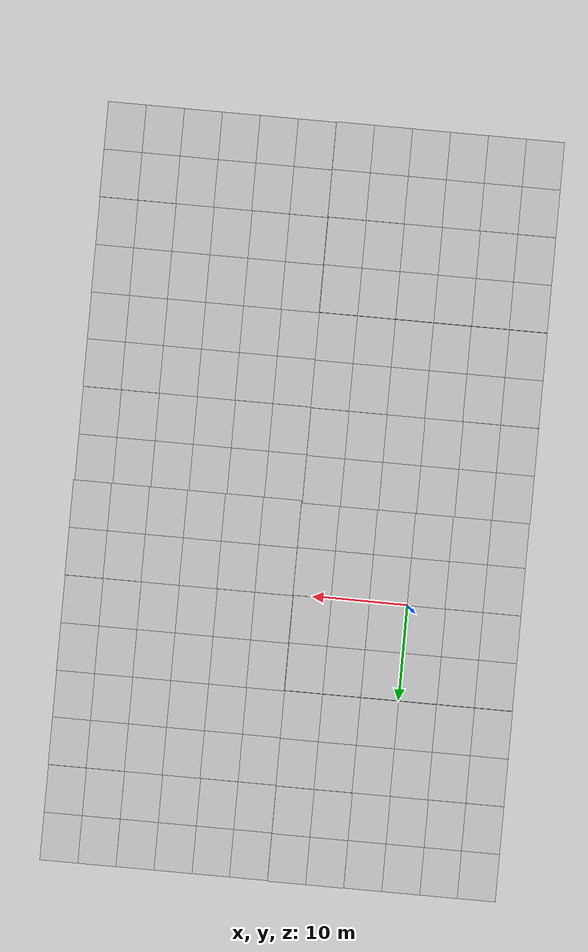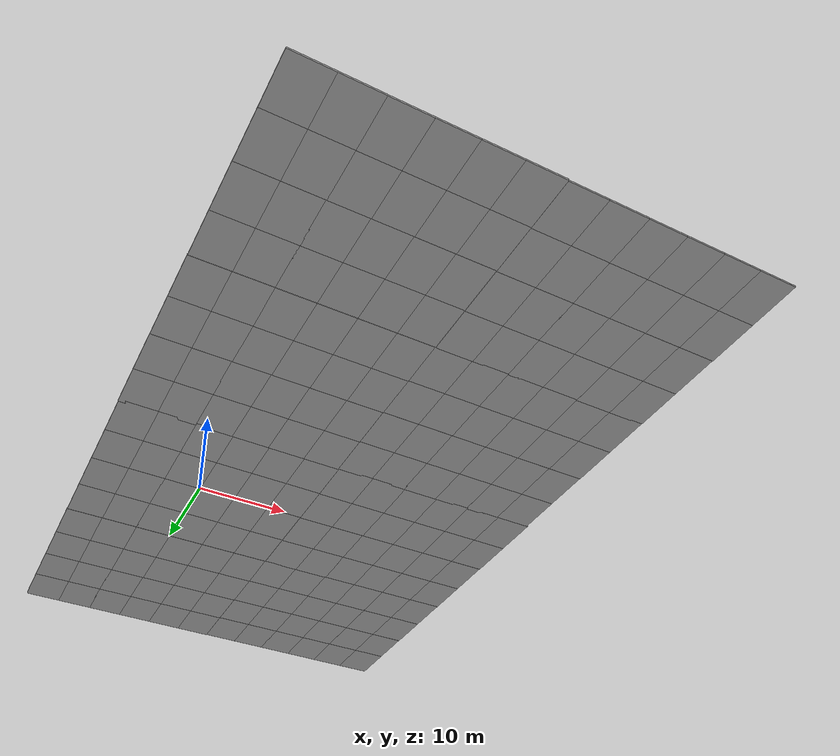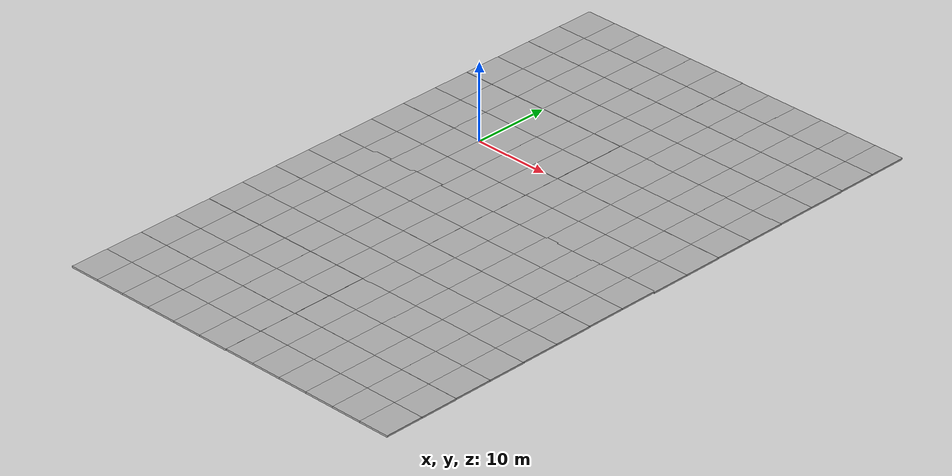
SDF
<?xml version='1.0'?>
<sdf version='1.6'>
  <model name='big_mud'>
    <model name='big_mud'>
      <model name='mud_box'>
        <static>1</static>
        <link name='link'>
          <collision name='collision'>
            <geometry>
              <box>
                <size>100 100 0.2</size>
              </box>
            </geometry>
          </collision>
          <visual name='visual_1'>
            <pose frame=''>-2 2.5 0 0 -0 0</pose>
            <cast_shadows>0</cast_shadows>
            <geometry>
              <box>
                <size>4 5 0.2</size>
              </box>
            </geometry>
            <material>
              <script>
                <uri>model://mud_box/materials/scripts</uri>
                <uri>model://mud_box/materials/textures</uri>
                <name>vrc/mud</name>
              </script>
            </material>
          </visual>
          <visual name='visual_2'>
            <pose frame=''>2 2.5 0 0 -0 0</pose>
            <cast_shadows>0</cast_shadows>
            <geometry>
              <box>
                <size>4 5 0.2</size>
              </box>
            </geometry>
            <material>
              <script>
                <uri>model://mud_box/materials/scripts</uri>
                <uri>model://mud_box/materials/textures</uri>
                <name>vrc/mud</name>
              </script>
            </material>
          </visual>
          <visual name='visual_3'>
            <pose frame=''>2 -2.5 0 0 -0 0</pose>
            <cast_shadows>0</cast_shadows>
            <geometry>
              <box>
                <size>4 5 0.2</size>
              </box>
            </geometry>
            <material>
              <script>
                <uri>model://mud_box/materials/scripts</uri>
                <uri>model://mud_box/materials/textures</uri>
                <name>vrc/mud</name>
              </script>
            </material>
          </visual>
          <visual name='visual_4'>
            <pose frame=''>-2 -2.5 0 0 -0 0</pose>
            <cast_shadows>0</cast_shadows>
            <geometry>
              <box>
                <size>4 5 0.2</size>
              </box>
            </geometry>
            <material>
              <script>
                <uri>model://mud_box/materials/scripts</uri>
                <uri>model://mud_box/materials/textures</uri>
                <name>vrc/mud</name>
              </script>
            </material>
          </visual>
        </link>
        <pose frame=''>-0.040479 4.99985 0 0 -0 0</pose>
      </model>
      <model name='mud_box_0'>
        <static>1</static>
        <link name='link'>
          <collision name='collision'>
            <geometry>
              <box>
                <size>8 10 0.2</size>
              </box>
            </geometry>
          </collision>
          <visual name='visual_1'>
            <pose frame=''>-2 2.5 0 0 -0 0</pose>
            <cast_shadows>0</cast_shadows>
            <geometry>
              <box>
                <size>4 5 0.2</size>
              </box>
            </geometry>
            <material>
              <script>
                <uri>model://mud_box/materials/scripts</uri>
                <uri>model://mud_box/materials/textures</uri>
                <name>vrc/mud</name>
              </script>
            </material>
          </visual>
          <visual name='visual_2'>
            <pose frame=''>2 2.5 0 0 -0 0</pose>
            <cast_shadows>0</cast_shadows>
            <geometry>
              <box>
                <size>4 5 0.2</size>
              </box>
            </geometry>
            <material>
              <script>
                <uri>model://mud_box/materials/scripts</uri>
                <uri>model://mud_box/materials/textures</uri>
                <name>vrc/mud</name>
              </script>
            </material>
          </visual>
          <visual name='visual_3'>
            <pose frame=''>2 -2.5 0 0 -0 0</pose>
            <cast_shadows>0</cast_shadows>
            <geometry>
              <box>
                <size>4 5 0.2</size>
              </box>
            </geometry>
            <material>
              <script>
                <uri>model://mud_box/materials/scripts</uri>
                <uri>model://mud_box/materials/textures</uri>
                <name>vrc/mud</name>
              </script>
            </material>
          </visual>
          <visual name='visual_4'>
            <pose frame=''>-2 -2.5 0 0 -0 0</pose>
            <cast_shadows>0</cast_shadows>
            <geometry>
              <box>
                <size>4 5 0.2</size>
              </box>
            </geometry>
            <material>
              <script>
                <uri>model://mud_box/materials/scripts</uri>
                <uri>model://mud_box/materials/textures</uri>
                <name>vrc/mud</name>
              </script>
            </material>
          </visual>
        </link>
        <pose frame=''>7.96088 5.01054 0 0 -0 0</pose>
      </model>
      <model name='mud_box_clone'>
        <static>1</static>
        <link name='link'>
          <collision name='collision'>
            <geometry>
              <box>
                <size>8 10 0.2</size>
              </box>
            </geometry>
          </collision>
          <visual name='visual_1'>
            <pose frame=''>-2 2.5 0 0 -0 0</pose>
            <cast_shadows>0</cast_shadows>
            <geometry>
              <box>
                <size>4 5 0.2</size>
              </box>
            </geometry>
            <material>
              <script>
                <uri>model://mud_box/materials/scripts</uri>
                <uri>model://mud_box/materials/textures</uri>
                <name>vrc/mud</name>
              </script>
            </material>
          </visual>
          <visual name='visual_2'>
            <pose frame=''>2 2.5 0 0 -0 0</pose>
            <cast_shadows>0</cast_shadows>
            <geometry>
              <box>
                <size>4 5 0.2</size>
              </box>
            </geometry>
            <material>
              <script>
                <uri>model://mud_box/materials/scripts</uri>
                <uri>model://mud_box/materials/textures</uri>
                <name>vrc/mud</name>
              </script>
            </material>
          </visual>
          <visual name='visual_3'>
            <pose frame=''>2 -2.5 0 0 -0 0</pose>
            <cast_shadows>0</cast_shadows>
            <geometry>
              <box>
                <size>4 5 0.2</size>
              </box>
            </geometry>
            <material>
              <script>
                <uri>model://mud_box/materials/scripts</uri>
                <uri>model://mud_box/materials/textures</uri>
                <name>vrc/mud</name>
              </script>
            </material>
          </visual>
          <visual name='visual_4'>
            <pose frame=''>-2 -2.5 0 0 -0 0</pose>
            <cast_shadows>0</cast_shadows>
            <geometry>
              <box>
                <size>4 5 0.2</size>
              </box>
            </geometry>
            <material>
              <script>
                <uri>model://mud_box/materials/scripts</uri>
                <uri>model://mud_box/materials/textures</uri>
                <name>vrc/mud</name>
              </script>
            </material>
          </visual>
        </link>
        <pose frame=''>8.00404 -5.00098 0 0 -0 0</pose>
      </model>
      <model name='mud_box_clone_0'>
        <static>1</static>
        <link name='link'>
          <collision name='collision'>
            <geometry>
              <box>
                <size>8 10 0.2</size>
              </box>
            </geometry>
          </collision>
          <visual name='visual_1'>
            <pose frame=''>-2 2.5 0 0 -0 0</pose>
            <cast_shadows>0</cast_shadows>
            <geometry>
              <box>
                <size>4 5 0.2</size>
              </box>
            </geometry>
            <material>
              <script>
                <uri>model://mud_box/materials/scripts</uri>
                <uri>model://mud_box/materials/textures</uri>
                <name>vrc/mud</name>
              </script>
            </material>
          </visual>
          <visual name='visual_2'>
            <pose frame=''>2 2.5 0 0 -0 0</pose>
            <cast_shadows>0</cast_shadows>
            <geometry>
              <box>
                <size>4 5 0.2</size>
              </box>
            </geometry>
            <material>
              <script>
                <uri>model://mud_box/materials/scripts</uri>
                <uri>model://mud_box/materials/textures</uri>
                <name>vrc/mud</name>
              </script>
            </material>
          </visual>
          <visual name='visual_3'>
            <pose frame=''>2 -2.5 0 0 -0 0</pose>
            <cast_shadows>0</cast_shadows>
            <geometry>
              <box>
                <size>4 5 0.2</size>
              </box>
            </geometry>
            <material>
              <script>
                <uri>model://mud_box/materials/scripts</uri>
                <uri>model://mud_box/materials/textures</uri>
                <name>vrc/mud</name>
              </script>
            </material>
          </visual>
          <visual name='visual_4'>
            <pose frame=''>-2 -2.5 0 0 -0 0</pose>
            <cast_shadows>0</cast_shadows>
            <geometry>
              <box>
                <size>4 5 0.2</size>
              </box>
            </geometry>
            <material>
              <script>
                <uri>model://mud_box/materials/scripts</uri>
                <uri>model://mud_box/materials/textures</uri>
                <name>vrc/mud</name>
              </script>
            </material>
          </visual>
        </link>
        <pose frame=''>-7.97159 4.99756 0 0 -0 0</pose>
      </model>
      <model name='mud_box_clone_0_clone'>
        <static>1</static>
        <link name='link'>
          <collision name='collision'>
            <geometry>
              <box>
                <size>8 10 0.2</size>
              </box>
            </geometry>
          </collision>
          <visual name='visual_1'>
            <pose frame=''>-2 2.5 0 0 -0 0</pose>
            <cast_shadows>0</cast_shadows>
            <geometry>
              <box>
                <size>4 5 0.2</size>
              </box>
            </geometry>
            <material>
              <script>
                <uri>model://mud_box/materials/scripts</uri>
                <uri>model://mud_box/materials/textures</uri>
                <name>vrc/mud</name>
              </script>
            </material>
          </visual>
          <visual name='visual_2'>
            <pose frame=''>2 2.5 0 0 -0 0</pose>
            <cast_shadows>0</cast_shadows>
            <geometry>
              <box>
                <size>4 5 0.2</size>
              </box>
            </geometry>
            <material>
              <script>
                <uri>model://mud_box/materials/scripts</uri>
                <uri>model://mud_box/materials/textures</uri>
                <name>vrc/mud</name>
              </script>
            </material>
          </visual>
          <visual name='visual_3'>
            <pose frame=''>2 -2.5 0 0 -0 0</pose>
            <cast_shadows>0</cast_shadows>
            <geometry>
              <box>
                <size>4 5 0.2</size>
              </box>
            </geometry>
            <material>
              <script>
                <uri>model://mud_box/materials/scripts</uri>
                <uri>model://mud_box/materials/textures</uri>
                <name>vrc/mud</name>
              </script>
            </material>
          </visual>
          <visual name='visual_4'>
            <pose frame=''>-2 -2.5 0 0 -0 0</pose>
            <cast_shadows>0</cast_shadows>
            <geometry>
              <box>
                <size>4 5 0.2</size>
              </box>
            </geometry>
            <material>
              <script>
                <uri>model://mud_box/materials/scripts</uri>
                <uri>model://mud_box/materials/textures</uri>
                <name>vrc/mud</name>
              </script>
            </material>
          </visual>
        </link>
        <pose frame=''>-7.96387 -5.00926 0 0 -0 0</pose>
      </model>
      <model name='mud_box_clone_clone'>
        <static>1</static>
        <link name='link'>
          <collision name='collision'>
            <geometry>
              <box>
                <size>8 10 0.2</size>
              </box>
            </geometry>
          </collision>
          <visual name='visual_1'>
            <pose frame=''>-2 2.5 0 0 -0 0</pose>
            <cast_shadows>0</cast_shadows>
            <geometry>
              <box>
                <size>4 5 0.2</size>
              </box>
            </geometry>
            <material>
              <script>
                <uri>model://mud_box/materials/scripts</uri>
                <uri>model://mud_box/materials/textures</uri>
                <name>vrc/mud</name>
              </script>
            </material>
          </visual>
          <visual name='visual_2'>
            <pose frame=''>2 2.5 0 0 -0 0</pose>
            <cast_shadows>0</cast_shadows>
            <geometry>
              <box>
                <size>4 5 0.2</size>
              </box>
            </geometry>
            <material>
              <script>
                <uri>model://mud_box/materials/scripts</uri>
                <uri>model://mud_box/materials/textures</uri>
                <name>vrc/mud</name>
              </script>
            </material>
          </visual>
          <visual name='visual_3'>
            <pose frame=''>2 -2.5 0 0 -0 0</pose>
            <cast_shadows>0</cast_shadows>
            <geometry>
              <box>
                <size>4 5 0.2</size>
              </box>
            </geometry>
            <material>
              <script>
                <uri>model://mud_box/materials/scripts</uri>
                <uri>model://mud_box/materials/textures</uri>
                <name>vrc/mud</name>
              </script>
            </material>
          </visual>
          <visual name='visual_4'>
            <pose frame=''>-2 -2.5 0 0 -0 0</pose>
            <cast_shadows>0</cast_shadows>
            <geometry>
              <box>
                <size>4 5 0.2</size>
              </box>
            </geometry>
            <material>
              <script>
                <uri>model://mud_box/materials/scripts</uri>
                <uri>model://mud_box/materials/textures</uri>
                <name>vrc/mud</name>
              </script>
            </material>
          </visual>
        </link>
        <pose frame=''>0.011012 -4.9977 0 0 -0 0</pose>
      </model>
      <static>0</static>
      <allow_auto_disable>1</allow_auto_disable>
      <pose frame=''>-0.037889 20.0397 0 0 -0 0</pose>
    </model>
    <model name='big_mud_0'>
      <model name='mud_box'>
        <static>1</static>
        <link name='link'>
          <collision name='collision'>
            <geometry>
              <box>
                <size>8 10 0.2</size>
              </box>
            </geometry>
          </collision>
          <visual name='visual_1'>
            <pose frame=''>-2 2.5 0 0 -0 0</pose>
            <cast_shadows>0</cast_shadows>
            <geometry>
              <box>
                <size>4 5 0.2</size>
              </box>
            </geometry>
            <material>
              <script>
                <uri>model://mud_box/materials/scripts</uri>
                <uri>model://mud_box/materials/textures</uri>
                <name>vrc/mud</name>
              </script>
            </material>
          </visual>
          <visual name='visual_2'>
            <pose frame=''>2 2.5 0 0 -0 0</pose>
            <cast_shadows>0</cast_shadows>
            <geometry>
              <box>
                <size>4 5 0.2</size>
              </box>
            </geometry>
            <material>
              <script>
                <uri>model://mud_box/materials/scripts</uri>
                <uri>model://mud_box/materials/textures</uri>
                <name>vrc/mud</name>
              </script>
            </material>
          </visual>
          <visual name='visual_3'>
            <pose frame=''>2 -2.5 0 0 -0 0</pose>
            <cast_shadows>0</cast_shadows>
            <geometry>
              <box>
                <size>4 5 0.2</size>
              </box>
            </geometry>
            <material>
              <script>
                <uri>model://mud_box/materials/scripts</uri>
                <uri>model://mud_box/materials/textures</uri>
                <name>vrc/mud</name>
              </script>
            </material>
          </visual>
          <visual name='visual_4'>
            <pose frame=''>-2 -2.5 0 0 -0 0</pose>
            <cast_shadows>0</cast_shadows>
            <geometry>
              <box>
                <size>4 5 0.2</size>
              </box>
            </geometry>
            <material>
              <script>
                <uri>model://mud_box/materials/scripts</uri>
                <uri>model://mud_box/materials/textures</uri>
                <name>vrc/mud</name>
              </script>
            </material>
          </visual>
        </link>
        <pose frame=''>-0.040479 4.99985 0 0 -0 0</pose>
      </model>
      <model name='mud_box_0'>
        <static>1</static>
        <link name='link'>
          <collision name='collision'>
            <geometry>
              <box>
                <size>8 10 0.2</size>
              </box>
            </geometry>
          </collision>
          <visual name='visual_1'>
            <pose frame=''>-2 2.5 0 0 -0 0</pose>
            <cast_shadows>0</cast_shadows>
            <geometry>
              <box>
                <size>4 5 0.2</size>
              </box>
            </geometry>
            <material>
              <script>
                <uri>model://mud_box/materials/scripts</uri>
                <uri>model://mud_box/materials/textures</uri>
                <name>vrc/mud</name>
              </script>
            </material>
          </visual>
          <visual name='visual_2'>
            <pose frame=''>2 2.5 0 0 -0 0</pose>
            <cast_shadows>0</cast_shadows>
            <geometry>
              <box>
                <size>4 5 0.2</size>
              </box>
            </geometry>
            <material>
              <script>
                <uri>model://mud_box/materials/scripts</uri>
                <uri>model://mud_box/materials/textures</uri>
                <name>vrc/mud</name>
              </script>
            </material>
          </visual>
          <visual name='visual_3'>
            <pose frame=''>2 -2.5 0 0 -0 0</pose>
            <cast_shadows>0</cast_shadows>
            <geometry>
              <box>
                <size>4 5 0.2</size>
              </box>
            </geometry>
            <material>
              <script>
                <uri>model://mud_box/materials/scripts</uri>
                <uri>model://mud_box/materials/textures</uri>
                <name>vrc/mud</name>
              </script>
            </material>
          </visual>
          <visual name='visual_4'>
            <pose frame=''>-2 -2.5 0 0 -0 0</pose>
            <cast_shadows>0</cast_shadows>
            <geometry>
              <box>
                <size>4 5 0.2</size>
              </box>
            </geometry>
            <material>
              <script>
                <uri>model://mud_box/materials/scripts</uri>
                <uri>model://mud_box/materials/textures</uri>
                <name>vrc/mud</name>
              </script>
            </material>
          </visual>
        </link>
        <pose frame=''>7.96088 5.01054 0 0 -0 0</pose>
      </model>
      <model name='mud_box_clone'>
        <static>1</static>
        <link name='link'>
          <collision name='collision'>
            <geometry>
              <box>
                <size>8 10 0.2</size>
              </box>
            </geometry>
          </collision>
          <visual name='visual_1'>
            <pose frame=''>-2 2.5 0 0 -0 0</pose>
            <cast_shadows>0</cast_shadows>
            <geometry>
              <box>
                <size>4 5 0.2</size>
              </box>
            </geometry>
            <material>
              <script>
                <uri>model://mud_box/materials/scripts</uri>
                <uri>model://mud_box/materials/textures</uri>
                <name>vrc/mud</name>
              </script>
            </material>
          </visual>
          <visual name='visual_2'>
            <pose frame=''>2 2.5 0 0 -0 0</pose>
            <cast_shadows>0</cast_shadows>
            <geometry>
              <box>
                <size>4 5 0.2</size>
              </box>
            </geometry>
            <material>
              <script>
                <uri>model://mud_box/materials/scripts</uri>
                <uri>model://mud_box/materials/textures</uri>
                <name>vrc/mud</name>
              </script>
            </material>
          </visual>
          <visual name='visual_3'>
            <pose frame=''>2 -2.5 0 0 -0 0</pose>
            <cast_shadows>0</cast_shadows>
            <geometry>
              <box>
                <size>4 5 0.2</size>
              </box>
            </geometry>
            <material>
              <script>
                <uri>model://mud_box/materials/scripts</uri>
                <uri>model://mud_box/materials/textures</uri>
                <name>vrc/mud</name>
              </script>
            </material>
          </visual>
          <visual name='visual_4'>
            <pose frame=''>-2 -2.5 0 0 -0 0</pose>
            <cast_shadows>0</cast_shadows>
            <geometry>
              <box>
                <size>4 5 0.2</size>
              </box>
            </geometry>
            <material>
              <script>
                <uri>model://mud_box/materials/scripts</uri>
                <uri>model://mud_box/materials/textures</uri>
                <name>vrc/mud</name>
              </script>
            </material>
          </visual>
        </link>
        <pose frame=''>8.00404 -5.00098 0 0 -0 0</pose>
      </model>
      <model name='mud_box_clone_0'>
        <static>1</static>
        <link name='link'>
          <collision name='collision'>
            <geometry>
              <box>
                <size>8 10 0.2</size>
              </box>
            </geometry>
          </collision>
          <visual name='visual_1'>
            <pose frame=''>-2 2.5 0 0 -0 0</pose>
            <cast_shadows>0</cast_shadows>
            <geometry>
              <box>
                <size>4 5 0.2</size>
              </box>
            </geometry>
            <material>
              <script>
                <uri>model://mud_box/materials/scripts</uri>
                <uri>model://mud_box/materials/textures</uri>
                <name>vrc/mud</name>
              </script>
            </material>
          </visual>
          <visual name='visual_2'>
            <pose frame=''>2 2.5 0 0 -0 0</pose>
            <cast_shadows>0</cast_shadows>
            <geometry>
              <box>
                <size>4 5 0.2</size>
              </box>
            </geometry>
            <material>
              <script>
                <uri>model://mud_box/materials/scripts</uri>
                <uri>model://mud_box/materials/textures</uri>
                <name>vrc/mud</name>
              </script>
            </material>
          </visual>
          <visual name='visual_3'>
            <pose frame=''>2 -2.5 0 0 -0 0</pose>
            <cast_shadows>0</cast_shadows>
            <geometry>
              <box>
                <size>4 5 0.2</size>
              </box>
            </geometry>
            <material>
              <script>
                <uri>model://mud_box/materials/scripts</uri>
                <uri>model://mud_box/materials/textures</uri>
                <name>vrc/mud</name>
              </script>
            </material>
          </visual>
          <visual name='visual_4'>
            <pose frame=''>-2 -2.5 0 0 -0 0</pose>
            <cast_shadows>0</cast_shadows>
            <geometry>
              <box>
                <size>4 5 0.2</size>
              </box>
            </geometry>
            <material>
              <script>
                <uri>model://mud_box/materials/scripts</uri>
                <uri>model://mud_box/materials/textures</uri>
                <name>vrc/mud</name>
              </script>
            </material>
          </visual>
        </link>
        <pose frame=''>-7.97159 4.99756 0 0 -0 0</pose>
      </model>
      <model name='mud_box_clone_0_clone'>
        <static>1</static>
        <link name='link'>
          <collision name='collision'>
            <geometry>
              <box>
                <size>8 10 0.2</size>
              </box>
            </geometry>
          </collision>
          <visual name='visual_1'>
            <pose frame=''>-2 2.5 0 0 -0 0</pose>
            <cast_shadows>0</cast_shadows>
            <geometry>
              <box>
                <size>4 5 0.2</size>
              </box>
            </geometry>
            <material>
              <script>
                <uri>model://mud_box/materials/scripts</uri>
                <uri>model://mud_box/materials/textures</uri>
                <name>vrc/mud</name>
              </script>
            </material>
          </visual>
          <visual name='visual_2'>
            <pose frame=''>2 2.5 0 0 -0 0</pose>
            <cast_shadows>0</cast_shadows>
            <geometry>
              <box>
                <size>4 5 0.2</size>
              </box>
            </geometry>
            <material>
              <script>
                <uri>model://mud_box/materials/scripts</uri>
                <uri>model://mud_box/materials/textures</uri>
                <name>vrc/mud</name>
              </script>
            </material>
          </visual>
          <visual name='visual_3'>
            <pose frame=''>2 -2.5 0 0 -0 0</pose>
            <cast_shadows>0</cast_shadows>
            <geometry>
              <box>
                <size>4 5 0.2</size>
              </box>
            </geometry>
            <material>
              <script>
                <uri>model://mud_box/materials/scripts</uri>
                <uri>model://mud_box/materials/textures</uri>
                <name>vrc/mud</name>
              </script>
            </material>
          </visual>
          <visual name='visual_4'>
            <pose frame=''>-2 -2.5 0 0 -0 0</pose>
            <cast_shadows>0</cast_shadows>
            <geometry>
              <box>
                <size>4 5 0.2</size>
              </box>
            </geometry>
            <material>
              <script>
                <uri>model://mud_box/materials/scripts</uri>
                <uri>model://mud_box/materials/textures</uri>
                <name>vrc/mud</name>
              </script>
            </material>
          </visual>
        </link>
        <pose frame=''>-7.96387 -5.00926 0 0 -0 0</pose>
      </model>
      <model name='mud_box_clone_clone'>
        <static>1</static>
        <link name='link'>
          <collision name='collision'>
            <geometry>
              <box>
                <size>8 10 0.2</size>
              </box>
            </geometry>
          </collision>
          <visual name='visual_1'>
            <pose frame=''>-2 2.5 0 0 -0 0</pose>
            <cast_shadows>0</cast_shadows>
            <geometry>
              <box>
                <size>4 5 0.2</size>
              </box>
            </geometry>
            <material>
              <script>
                <uri>model://mud_box/materials/scripts</uri>
                <uri>model://mud_box/materials/textures</uri>
                <name>vrc/mud</name>
              </script>
            </material>
          </visual>
          <visual name='visual_2'>
            <pose frame=''>2 2.5 0 0 -0 0</pose>
            <cast_shadows>0</cast_shadows>
            <geometry>
              <box>
                <size>4 5 0.2</size>
              </box>
            </geometry>
            <material>
              <script>
                <uri>model://mud_box/materials/scripts</uri>
                <uri>model://mud_box/materials/textures</uri>
                <name>vrc/mud</name>
              </script>
            </material>
          </visual>
          <visual name='visual_3'>
            <pose frame=''>2 -2.5 0 0 -0 0</pose>
            <cast_shadows>0</cast_shadows>
            <geometry>
              <box>
                <size>4 5 0.2</size>
              </box>
            </geometry>
            <material>
              <script>
                <uri>model://mud_box/materials/scripts</uri>
                <uri>model://mud_box/materials/textures</uri>
                <name>vrc/mud</name>
              </script>
            </material>
          </visual>
          <visual name='visual_4'>
            <pose frame=''>-2 -2.5 0 0 -0 0</pose>
            <cast_shadows>0</cast_shadows>
            <geometry>
              <box>
                <size>4 5 0.2</size>
              </box>
            </geometry>
            <material>
              <script>
                <uri>model://mud_box/materials/scripts</uri>
                <uri>model://mud_box/materials/textures</uri>
                <name>vrc/mud</name>
              </script>
            </material>
          </visual>
        </link>
        <pose frame=''>0.011012 -4.9977 0 0 -0 0</pose>
      </model>
      <static>0</static>
      <allow_auto_disable>1</allow_auto_disable>
      <pose frame=''>23.9817 0.073412 0 0 -0 0</pose>
    </model>
    <model name='big_mud_1'>
      <model name='mud_box'>
        <static>1</static>
        <link name='link'>
          <collision name='collision'>
            <geometry>
              <box>
                <size>8 10 0.2</size>
              </box>
            </geometry>
          </collision>
          <visual name='visual_1'>
            <pose frame=''>-2 2.5 0 0 -0 0</pose>
            <cast_shadows>0</cast_shadows>
            <geometry>
              <box>
                <size>4 5 0.2</size>
              </box>
            </geometry>
            <material>
              <script>
                <uri>model://mud_box/materials/scripts</uri>
                <uri>model://mud_box/materials/textures</uri>
                <name>vrc/mud</name>
              </script>
            </material>
          </visual>
          <visual name='visual_2'>
            <pose frame=''>2 2.5 0 0 -0 0</pose>
            <cast_shadows>0</cast_shadows>
            <geometry>
              <box>
                <size>4 5 0.2</size>
              </box>
            </geometry>
            <material>
              <script>
                <uri>model://mud_box/materials/scripts</uri>
                <uri>model://mud_box/materials/textures</uri>
                <name>vrc/mud</name>
              </script>
            </material>
          </visual>
          <visual name='visual_3'>
            <pose frame=''>2 -2.5 0 0 -0 0</pose>
            <cast_shadows>0</cast_shadows>
            <geometry>
              <box>
                <size>4 5 0.2</size>
              </box>
            </geometry>
            <material>
              <script>
                <uri>model://mud_box/materials/scripts</uri>
                <uri>model://mud_box/materials/textures</uri>
                <name>vrc/mud</name>
              </script>
            </material>
          </visual>
          <visual name='visual_4'>
            <pose frame=''>-2 -2.5 0 0 -0 0</pose>
            <cast_shadows>0</cast_shadows>
            <geometry>
              <box>
                <size>4 5 0.2</size>
              </box>
            </geometry>
            <material>
              <script>
                <uri>model://mud_box/materials/scripts</uri>
                <uri>model://mud_box/materials/textures</uri>
                <name>vrc/mud</name>
              </script>
            </material>
          </visual>
        </link>
        <pose frame=''>-0.040479 4.99985 0 0 -0 0</pose>
      </model>
      <model name='mud_box_0'>
        <static>1</static>
        <link name='link'>
          <collision name='collision'>
            <geometry>
              <box>
                <size>8 10 0.2</size>
              </box>
            </geometry>
          </collision>
          <visual name='visual_1'>
            <pose frame=''>-2 2.5 0 0 -0 0</pose>
            <cast_shadows>0</cast_shadows>
            <geometry>
              <box>
                <size>4 5 0.2</size>
              </box>
            </geometry>
            <material>
              <script>
                <uri>model://mud_box/materials/scripts</uri>
                <uri>model://mud_box/materials/textures</uri>
                <name>vrc/mud</name>
              </script>
            </material>
          </visual>
          <visual name='visual_2'>
            <pose frame=''>2 2.5 0 0 -0 0</pose>
            <cast_shadows>0</cast_shadows>
            <geometry>
              <box>
                <size>4 5 0.2</size>
              </box>
            </geometry>
            <material>
              <script>
                <uri>model://mud_box/materials/scripts</uri>
                <uri>model://mud_box/materials/textures</uri>
                <name>vrc/mud</name>
              </script>
            </material>
          </visual>
          <visual name='visual_3'>
            <pose frame=''>2 -2.5 0 0 -0 0</pose>
            <cast_shadows>0</cast_shadows>
            <geometry>
              <box>
                <size>4 5 0.2</size>
              </box>
            </geometry>
            <material>
              <script>
                <uri>model://mud_box/materials/scripts</uri>
                <uri>model://mud_box/materials/textures</uri>
                <name>vrc/mud</name>
              </script>
            </material>
          </visual>
          <visual name='visual_4'>
            <pose frame=''>-2 -2.5 0 0 -0 0</pose>
            <cast_shadows>0</cast_shadows>
            <geometry>
              <box>
                <size>4 5 0.2</size>
              </box>
            </geometry>
            <material>
              <script>
                <uri>model://mud_box/materials/scripts</uri>
                <uri>model://mud_box/materials/textures</uri>
                <name>vrc/mud</name>
              </script>
            </material>
          </visual>
        </link>
        <pose frame=''>7.96088 5.01054 0 0 -0 0</pose>
      </model>
      <model name='mud_box_clone'>
        <static>1</static>
        <link name='link'>
          <collision name='collision'>
            <geometry>
              <box>
                <size>8 10 0.2</size>
              </box>
            </geometry>
          </collision>
          <visual name='visual_1'>
            <pose frame=''>-2 2.5 0 0 -0 0</pose>
            <cast_shadows>0</cast_shadows>
            <geometry>
              <box>
                <size>4 5 0.2</size>
              </box>
            </geometry>
            <material>
              <script>
                <uri>model://mud_box/materials/scripts</uri>
                <uri>model://mud_box/materials/textures</uri>
                <name>vrc/mud</name>
              </script>
            </material>
          </visual>
          <visual name='visual_2'>
            <pose frame=''>2 2.5 0 0 -0 0</pose>
            <cast_shadows>0</cast_shadows>
            <geometry>
              <box>
                <size>4 5 0.2</size>
              </box>
            </geometry>
            <material>
              <script>
                <uri>model://mud_box/materials/scripts</uri>
                <uri>model://mud_box/materials/textures</uri>
                <name>vrc/mud</name>
              </script>
            </material>
          </visual>
          <visual name='visual_3'>
            <pose frame=''>2 -2.5 0 0 -0 0</pose>
            <cast_shadows>0</cast_shadows>
            <geometry>
              <box>
                <size>4 5 0.2</size>
              </box>
            </geometry>
            <material>
              <script>
                <uri>model://mud_box/materials/scripts</uri>
                <uri>model://mud_box/materials/textures</uri>
                <name>vrc/mud</name>
              </script>
            </material>
          </visual>
          <visual name='visual_4'>
            <pose frame=''>-2 -2.5 0 0 -0 0</pose>
            <cast_shadows>0</cast_shadows>
            <geometry>
              <box>
                <size>4 5 0.2</size>
              </box>
            </geometry>
            <material>
              <script>
                <uri>model://mud_box/materials/scripts</uri>
                <uri>model://mud_box/materials/textures</uri>
                <name>vrc/mud</name>
              </script>
            </material>
          </visual>
        </link>
        <pose frame=''>8.00404 -5.00098 0 0 -0 0</pose>
      </model>
      <model name='mud_box_clone_0'>
        <static>1</static>
        <link name='link'>
          <collision name='collision'>
            <geometry>
              <box>
                <size>8 10 0.2</size>
              </box>
            </geometry>
          </collision>
          <visual name='visual_1'>
            <pose frame=''>-2 2.5 0 0 -0 0</pose>
            <cast_shadows>0</cast_shadows>
            <geometry>
              <box>
                <size>4 5 0.2</size>
              </box>
            </geometry>
            <material>
              <script>
                <uri>model://mud_box/materials/scripts</uri>
                <uri>model://mud_box/materials/textures</uri>
                <name>vrc/mud</name>
              </script>
            </material>
          </visual>
          <visual name='visual_2'>
            <pose frame=''>2 2.5 0 0 -0 0</pose>
            <cast_shadows>0</cast_shadows>
            <geometry>
              <box>
                <size>4 5 0.2</size>
              </box>
            </geometry>
            <material>
              <script>
                <uri>model://mud_box/materials/scripts</uri>
                <uri>model://mud_box/materials/textures</uri>
                <name>vrc/mud</name>
              </script>
            </material>
          </visual>
          <visual name='visual_3'>
            <pose frame=''>2 -2.5 0 0 -0 0</pose>
            <cast_shadows>0</cast_shadows>
            <geometry>
              <box>
                <size>4 5 0.2</size>
              </box>
            </geometry>
            <material>
              <script>
                <uri>model://mud_box/materials/scripts</uri>
                <uri>model://mud_box/materials/textures</uri>
                <name>vrc/mud</name>
              </script>
            </material>
          </visual>
          <visual name='visual_4'>
            <pose frame=''>-2 -2.5 0 0 -0 0</pose>
            <cast_shadows>0</cast_shadows>
            <geometry>
              <box>
                <size>4 5 0.2</size>
              </box>
            </geometry>
            <material>
              <script>
                <uri>model://mud_box/materials/scripts</uri>
                <uri>model://mud_box/materials/textures</uri>
                <name>vrc/mud</name>
              </script>
            </material>
          </visual>
        </link>
        <pose frame=''>-7.97159 4.99756 0 0 -0 0</pose>
      </model>
      <model name='mud_box_clone_0_clone'>
        <static>1</static>
        <link name='link'>
          <collision name='collision'>
            <geometry>
              <box>
                <size>8 10 0.2</size>
              </box>
            </geometry>
          </collision>
          <visual name='visual_1'>
            <pose frame=''>-2 2.5 0 0 -0 0</pose>
            <cast_shadows>0</cast_shadows>
            <geometry>
              <box>
                <size>4 5 0.2</size>
              </box>
            </geometry>
            <material>
              <script>
                <uri>model://mud_box/materials/scripts</uri>
                <uri>model://mud_box/materials/textures</uri>
                <name>vrc/mud</name>
              </script>
            </material>
          </visual>
          <visual name='visual_2'>
            <pose frame=''>2 2.5 0 0 -0 0</pose>
            <cast_shadows>0</cast_shadows>
            <geometry>
              <box>
                <size>4 5 0.2</size>
              </box>
            </geometry>
            <material>
              <script>
                <uri>model://mud_box/materials/scripts</uri>
                <uri>model://mud_box/materials/textures</uri>
                <name>vrc/mud</name>
              </script>
            </material>
          </visual>
          <visual name='visual_3'>
            <pose frame=''>2 -2.5 0 0 -0 0</pose>
            <cast_shadows>0</cast_shadows>
            <geometry>
              <box>
                <size>4 5 0.2</size>
              </box>
            </geometry>
            <material>
              <script>
                <uri>model://mud_box/materials/scripts</uri>
                <uri>model://mud_box/materials/textures</uri>
                <name>vrc/mud</name>
              </script>
            </material>
          </visual>
          <visual name='visual_4'>
            <pose frame=''>-2 -2.5 0 0 -0 0</pose>
            <cast_shadows>0</cast_shadows>
            <geometry>
              <box>
                <size>4 5 0.2</size>
              </box>
            </geometry>
            <material>
              <script>
                <uri>model://mud_box/materials/scripts</uri>
                <uri>model://mud_box/materials/textures</uri>
                <name>vrc/mud</name>
              </script>
            </material>
          </visual>
        </link>
        <pose frame=''>-7.96387 -5.00926 0 0 -0 0</pose>
      </model>
      <model name='mud_box_clone_clone'>
        <static>1</static>
        <link name='link'>
          <collision name='collision'>
            <geometry>
              <box>
                <size>8 10 0.2</size>
              </box>
            </geometry>
          </collision>
          <visual name='visual_1'>
            <pose frame=''>-2 2.5 0 0 -0 0</pose>
            <cast_shadows>0</cast_shadows>
            <geometry>
              <box>
                <size>4 5 0.2</size>
              </box>
            </geometry>
            <material>
              <script>
                <uri>model://mud_box/materials/scripts</uri>
                <uri>model://mud_box/materials/textures</uri>
                <name>vrc/mud</name>
              </script>
            </material>
          </visual>
          <visual name='visual_2'>
            <pose frame=''>2 2.5 0 0 -0 0</pose>
            <cast_shadows>0</cast_shadows>
            <geometry>
              <box>
                <size>4 5 0.2</size>
              </box>
            </geometry>
            <material>
              <script>
                <uri>model://mud_box/materials/scripts</uri>
                <uri>model://mud_box/materials/textures</uri>
                <name>vrc/mud</name>
              </script>
            </material>
          </visual>
          <visual name='visual_3'>
            <pose frame=''>2 -2.5 0 0 -0 0</pose>
            <cast_shadows>0</cast_shadows>
            <geometry>
              <box>
                <size>4 5 0.2</size>
              </box>
            </geometry>
            <material>
              <script>
                <uri>model://mud_box/materials/scripts</uri>
                <uri>model://mud_box/materials/textures</uri>
                <name>vrc/mud</name>
              </script>
            </material>
          </visual>
          <visual name='visual_4'>
            <pose frame=''>-2 -2.5 0 0 -0 0</pose>
            <cast_shadows>0</cast_shadows>
            <geometry>
              <box>
                <size>4 5 0.2</size>
              </box>
            </geometry>
            <material>
              <script>
                <uri>model://mud_box/materials/scripts</uri>
                <uri>model://mud_box/materials/textures</uri>
                <name>vrc/mud</name>
              </script>
            </material>
          </visual>
        </link>
        <pose frame=''>0.011012 -4.9977 0 0 -0 0</pose>
      </model>
      <static>0</static>
      <allow_auto_disable>1</allow_auto_disable>
      <pose frame=''>23.9065 19.9843 0 0 -0 0</pose>
    </model>
    <model name='big_mud_2'>
      <model name='big_mud'>
        <model name='mud_box'>
          <static>1</static>
          <link name='link'>
            <collision name='collision'>
              <geometry>
                <box>
                  <size>8 10 0.2</size>
                </box>
              </geometry>
            </collision>
            <visual name='visual_1'>
              <pose frame=''>-2 2.5 0 0 -0 0</pose>
              <cast_shadows>0</cast_shadows>
              <geometry>
                <box>
                  <size>4 5 0.2</size>
                </box>
              </geometry>
              <material>
                <script>
                  <uri>model://mud_box/materials/scripts</uri>
                  <uri>model://mud_box/materials/textures</uri>
                  <name>vrc/mud</name>
                </script>
              </material>
            </visual>
            <visual name='visual_2'>
              <pose frame=''>2 2.5 0 0 -0 0</pose>
              <cast_shadows>0</cast_shadows>
              <geometry>
                <box>
                  <size>4 5 0.2</size>
                </box>
              </geometry>
              <material>
                <script>
                  <uri>model://mud_box/materials/scripts</uri>
                  <uri>model://mud_box/materials/textures</uri>
                  <name>vrc/mud</name>
                </script>
              </material>
            </visual>
            <visual name='visual_3'>
              <pose frame=''>2 -2.5 0 0 -0 0</pose>
              <cast_shadows>0</cast_shadows>
              <geometry>
                <box>
                  <size>4 5 0.2</size>
                </box>
              </geometry>
              <material>
                <script>
                  <uri>model://mud_box/materials/scripts</uri>
                  <uri>model://mud_box/materials/textures</uri>
                  <name>vrc/mud</name>
                </script>
              </material>
            </visual>
            <visual name='visual_4'>
              <pose frame=''>-2 -2.5 0 0 -0 0</pose>
              <cast_shadows>0</cast_shadows>
              <geometry>
                <box>
                  <size>4 5 0.2</size>
                </box>
              </geometry>
              <material>
                <script>
                  <uri>model://mud_box/materials/scripts</uri>
                  <uri>model://mud_box/materials/textures</uri>
                  <name>vrc/mud</name>
                </script>
              </material>
            </visual>
          </link>
          <pose frame=''>-0.040479 4.99985 0 0 -0 0</pose>
        </model>
        <model name='mud_box_0'>
          <static>1</static>
          <link name='link'>
            <collision name='collision'>
              <geometry>
                <box>
                  <size>8 10 0.2</size>
                </box>
              </geometry>
            </collision>
            <visual name='visual_1'>
              <pose frame=''>-2 2.5 0 0 -0 0</pose>
              <cast_shadows>0</cast_shadows>
              <geometry>
                <box>
                  <size>4 5 0.2</size>
                </box>
              </geometry>
              <material>
                <script>
                  <uri>model://mud_box/materials/scripts</uri>
                  <uri>model://mud_box/materials/textures</uri>
                  <name>vrc/mud</name>
                </script>
              </material>
            </visual>
            <visual name='visual_2'>
              <pose frame=''>2 2.5 0 0 -0 0</pose>
              <cast_shadows>0</cast_shadows>
              <geometry>
                <box>
                  <size>4 5 0.2</size>
                </box>
              </geometry>
              <material>
                <script>
                  <uri>model://mud_box/materials/scripts</uri>
                  <uri>model://mud_box/materials/textures</uri>
                  <name>vrc/mud</name>
                </script>
              </material>
            </visual>
            <visual name='visual_3'>
              <pose frame=''>2 -2.5 0 0 -0 0</pose>
              <cast_shadows>0</cast_shadows>
              <geometry>
                <box>
                  <size>4 5 0.2</size>
                </box>
              </geometry>
              <material>
                <script>
                  <uri>model://mud_box/materials/scripts</uri>
                  <uri>model://mud_box/materials/textures</uri>
                  <name>vrc/mud</name>
                </script>
              </material>
            </visual>
            <visual name='visual_4'>
              <pose frame=''>-2 -2.5 0 0 -0 0</pose>
              <cast_shadows>0</cast_shadows>
              <geometry>
                <box>
                  <size>4 5 0.2</size>
                </box>
              </geometry>
              <material>
                <script>
                  <uri>model://mud_box/materials/scripts</uri>
                  <uri>model://mud_box/materials/textures</uri>
                  <name>vrc/mud</name>
                </script>
              </material>
            </visual>
          </link>
          <pose frame=''>7.96088 5.01054 0 0 -0 0</pose>
        </model>
        <model name='mud_box_clone'>
          <static>1</static>
          <link name='link'>
            <collision name='collision'>
              <geometry>
                <box>
                  <size>8 10 0.2</size>
                </box>
              </geometry>
            </collision>
            <visual name='visual_1'>
              <pose frame=''>-2 2.5 0 0 -0 0</pose>
              <cast_shadows>0</cast_shadows>
              <geometry>
                <box>
                  <size>4 5 0.2</size>
                </box>
              </geometry>
              <material>
                <script>
                  <uri>model://mud_box/materials/scripts</uri>
                  <uri>model://mud_box/materials/textures</uri>
                  <name>vrc/mud</name>
                </script>
              </material>
            </visual>
            <visual name='visual_2'>
              <pose frame=''>2 2.5 0 0 -0 0</pose>
              <cast_shadows>0</cast_shadows>
              <geometry>
                <box>
                  <size>4 5 0.2</size>
                </box>
              </geometry>
              <material>
                <script>
                  <uri>model://mud_box/materials/scripts</uri>
                  <uri>model://mud_box/materials/textures</uri>
                  <name>vrc/mud</name>
                </script>
              </material>
            </visual>
            <visual name='visual_3'>
              <pose frame=''>2 -2.5 0 0 -0 0</pose>
              <cast_shadows>0</cast_shadows>
              <geometry>
                <box>
                  <size>4 5 0.2</size>
                </box>
              </geometry>
              <material>
                <script>
                  <uri>model://mud_box/materials/scripts</uri>
                  <uri>model://mud_box/materials/textures</uri>
                  <name>vrc/mud</name>
                </script>
              </material>
            </visual>
            <visual name='visual_4'>
              <pose frame=''>-2 -2.5 0 0 -0 0</pose>
              <cast_shadows>0</cast_shadows>
              <geometry>
                <box>
                  <size>4 5 0.2</size>
                </box>
              </geometry>
              <material>
                <script>
                  <uri>model://mud_box/materials/scripts</uri>
                  <uri>model://mud_box/materials/textures</uri>
                  <name>vrc/mud</name>
                </script>
              </material>
            </visual>
          </link>
          <pose frame=''>8.00404 -5.00098 0 0 -0 0</pose>
        </model>
        <model name='mud_box_clone_0'>
          <static>1</static>
          <link name='link'>
            <collision name='collision'>
              <geometry>
                <box>
                  <size>8 10 0.2</size>
                </box>
              </geometry>
            </collision>
            <visual name='visual_1'>
              <pose frame=''>-2 2.5 0 0 -0 0</pose>
              <cast_shadows>0</cast_shadows>
              <geometry>
                <box>
                  <size>4 5 0.2</size>
                </box>
              </geometry>
              <material>
                <script>
                  <uri>model://mud_box/materials/scripts</uri>
                  <uri>model://mud_box/materials/textures</uri>
                  <name>vrc/mud</name>
                </script>
              </material>
            </visual>
            <visual name='visual_2'>
              <pose frame=''>2 2.5 0 0 -0 0</pose>
              <cast_shadows>0</cast_shadows>
              <geometry>
                <box>
                  <size>4 5 0.2</size>
                </box>
              </geometry>
              <material>
                <script>
                  <uri>model://mud_box/materials/scripts</uri>
                  <uri>model://mud_box/materials/textures</uri>
                  <name>vrc/mud</name>
                </script>
              </material>
            </visual>
            <visual name='visual_3'>
              <pose frame=''>2 -2.5 0 0 -0 0</pose>
              <cast_shadows>0</cast_shadows>
              <geometry>
                <box>
                  <size>4 5 0.2</size>
                </box>
              </geometry>
              <material>
                <script>
                  <uri>model://mud_box/materials/scripts</uri>
                  <uri>model://mud_box/materials/textures</uri>
                  <name>vrc/mud</name>
                </script>
              </material>
            </visual>
            <visual name='visual_4'>
              <pose frame=''>-2 -2.5 0 0 -0 0</pose>
              <cast_shadows>0</cast_shadows>
              <geometry>
                <box>
                  <size>4 5 0.2</size>
                </box>
              </geometry>
              <material>
                <script>
                  <uri>model://mud_box/materials/scripts</uri>
                  <uri>model://mud_box/materials/textures</uri>
                  <name>vrc/mud</name>
                </script>
              </material>
            </visual>
          </link>
          <pose frame=''>-7.97159 4.99756 0 0 -0 0</pose>
        </model>
        <model name='mud_box_clone_0_clone'>
          <static>1</static>
          <link name='link'>
            <collision name='collision'>
              <geometry>
                <box>
                  <size>8 10 0.2</size>
                </box>
              </geometry>
            </collision>
            <visual name='visual_1'>
              <pose frame=''>-2 2.5 0 0 -0 0</pose>
              <cast_shadows>0</cast_shadows>
              <geometry>
                <box>
                  <size>4 5 0.2</size>
                </box>
              </geometry>
              <material>
                <script>
                  <uri>model://mud_box/materials/scripts</uri>
                  <uri>model://mud_box/materials/textures</uri>
                  <name>vrc/mud</name>
                </script>
              </material>
            </visual>
            <visual name='visual_2'>
              <pose frame=''>2 2.5 0 0 -0 0</pose>
              <cast_shadows>0</cast_shadows>
              <geometry>
                <box>
                  <size>4 5 0.2</size>
                </box>
              </geometry>
              <material>
                <script>
                  <uri>model://mud_box/materials/scripts</uri>
                  <uri>model://mud_box/materials/textures</uri>
                  <name>vrc/mud</name>
                </script>
              </material>
            </visual>
            <visual name='visual_3'>
              <pose frame=''>2 -2.5 0 0 -0 0</pose>
              <cast_shadows>0</cast_shadows>
              <geometry>
                <box>
                  <size>4 5 0.2</size>
                </box>
              </geometry>
              <material>
                <script>
                  <uri>model://mud_box/materials/scripts</uri>
                  <uri>model://mud_box/materials/textures</uri>
                  <name>vrc/mud</name>
                </script>
              </material>
            </visual>
            <visual name='visual_4'>
              <pose frame=''>-2 -2.5 0 0 -0 0</pose>
              <cast_shadows>0</cast_shadows>
              <geometry>
                <box>
                  <size>4 5 0.2</size>
                </box>
              </geometry>
              <material>
                <script>
                  <uri>model://mud_box/materials/scripts</uri>
                  <uri>model://mud_box/materials/textures</uri>
                  <name>vrc/mud</name>
                </script>
              </material>
            </visual>
          </link>
          <pose frame=''>-7.96387 -5.00926 0 0 -0 0</pose>
        </model>
        <model name='mud_box_clone_clone'>
          <static>1</static>
          <link name='link'>
            <collision name='collision'>
              <geometry>
                <box>
                  <size>8 10 0.2</size>
                </box>
              </geometry>
            </collision>
            <visual name='visual_1'>
              <pose frame=''>-2 2.5 0 0 -0 0</pose>
              <cast_shadows>0</cast_shadows>
              <geometry>
                <box>
                  <size>4 5 0.2</size>
                </box>
              </geometry>
              <material>
                <script>
                  <uri>model://mud_box/materials/scripts</uri>
                  <uri>model://mud_box/materials/textures</uri>
                  <name>vrc/mud</name>
                </script>
              </material>
            </visual>
            <visual name='visual_2'>
              <pose frame=''>2 2.5 0 0 -0 0</pose>
              <cast_shadows>0</cast_shadows>
              <geometry>
                <box>
                  <size>4 5 0.2</size>
                </box>
              </geometry>
              <material>
                <script>
                  <uri>model://mud_box/materials/scripts</uri>
                  <uri>model://mud_box/materials/textures</uri>
                  <name>vrc/mud</name>
                </script>
              </material>
            </visual>
            <visual name='visual_3'>
              <pose frame=''>2 -2.5 0 0 -0 0</pose>
              <cast_shadows>0</cast_shadows>
              <geometry>
                <box>
                  <size>4 5 0.2</size>
                </box>
              </geometry>
              <material>
                <script>
                  <uri>model://mud_box/materials/scripts</uri>
                  <uri>model://mud_box/materials/textures</uri>
                  <name>vrc/mud</name>
                </script>
              </material>
            </visual>
            <visual name='visual_4'>
              <pose frame=''>-2 -2.5 0 0 -0 0</pose>
              <cast_shadows>0</cast_shadows>
              <geometry>
                <box>
                  <size>4 5 0.2</size>
                </box>
              </geometry>
              <material>
                <script>
                  <uri>model://mud_box/materials/scripts</uri>
                  <uri>model://mud_box/materials/textures</uri>
                  <name>vrc/mud</name>
                </script>
              </material>
            </visual>
          </link>
          <pose frame=''>0.011012 -4.9977 0 0 -0 0</pose>
        </model>
        <static>0</static>
        <allow_auto_disable>1</allow_auto_disable>
        <pose frame=''>-0.037889 20.0397 0 0 -0 0</pose>
      </model>
      <model name='big_mud_0'>
        <model name='mud_box'>
          <static>1</static>
          <link name='link'>
            <collision name='collision'>
              <geometry>
                <box>
                  <size>8 10 0.2</size>
                </box>
              </geometry>
            </collision>
            <visual name='visual_1'>
              <pose frame=''>-2 2.5 0 0 -0 0</pose>
              <cast_shadows>0</cast_shadows>
              <geometry>
                <box>
                  <size>4 5 0.2</size>
                </box>
              </geometry>
              <material>
                <script>
                  <uri>model://mud_box/materials/scripts</uri>
                  <uri>model://mud_box/materials/textures</uri>
                  <name>vrc/mud</name>
                </script>
              </material>
            </visual>
            <visual name='visual_2'>
              <pose frame=''>2 2.5 0 0 -0 0</pose>
              <cast_shadows>0</cast_shadows>
              <geometry>
                <box>
                  <size>4 5 0.2</size>
                </box>
              </geometry>
              <material>
                <script>
                  <uri>model://mud_box/materials/scripts</uri>
                  <uri>model://mud_box/materials/textures</uri>
                  <name>vrc/mud</name>
                </script>
              </material>
            </visual>
            <visual name='visual_3'>
              <pose frame=''>2 -2.5 0 0 -0 0</pose>
              <cast_shadows>0</cast_shadows>
              <geometry>
                <box>
                  <size>4 5 0.2</size>
                </box>
              </geometry>
              <material>
                <script>
                  <uri>model://mud_box/materials/scripts</uri>
                  <uri>model://mud_box/materials/textures</uri>
                  <name>vrc/mud</name>
                </script>
              </material>
            </visual>
            <visual name='visual_4'>
              <pose frame=''>-2 -2.5 0 0 -0 0</pose>
              <cast_shadows>0</cast_shadows>
              <geometry>
                <box>
                  <size>4 5 0.2</size>
                </box>
              </geometry>
              <material>
                <script>
                  <uri>model://mud_box/materials/scripts</uri>
                  <uri>model://mud_box/materials/textures</uri>
                  <name>vrc/mud</name>
                </script>
              </material>
            </visual>
          </link>
          <pose frame=''>-0.040479 4.99985 0 0 -0 0</pose>
        </model>
        <model name='mud_box_0'>
          <static>1</static>
          <link name='link'>
            <collision name='collision'>
              <geometry>
                <box>
                  <size>8 10 0.2</size>
                </box>
              </geometry>
            </collision>
            <visual name='visual_1'>
              <pose frame=''>-2 2.5 0 0 -0 0</pose>
              <cast_shadows>0</cast_shadows>
              <geometry>
                <box>
                  <size>4 5 0.2</size>
                </box>
              </geometry>
              <material>
                <script>
                  <uri>model://mud_box/materials/scripts</uri>
                  <uri>model://mud_box/materials/textures</uri>
                  <name>vrc/mud</name>
                </script>
              </material>
            </visual>
            <visual name='visual_2'>
              <pose frame=''>2 2.5 0 0 -0 0</pose>
              <cast_shadows>0</cast_shadows>
              <geometry>
                <box>
                  <size>4 5 0.2</size>
                </box>
              </geometry>
              <material>
                <script>
                  <uri>model://mud_box/materials/scripts</uri>
                  <uri>model://mud_box/materials/textures</uri>
                  <name>vrc/mud</name>
                </script>
              </material>
            </visual>
            <visual name='visual_3'>
              <pose frame=''>2 -2.5 0 0 -0 0</pose>
              <cast_shadows>0</cast_shadows>
              <geometry>
                <box>
                  <size>4 5 0.2</size>
                </box>
              </geometry>
              <material>
                <script>
                  <uri>model://mud_box/materials/scripts</uri>
                  <uri>model://mud_box/materials/textures</uri>
                  <name>vrc/mud</name>
                </script>
              </material>
            </visual>
            <visual name='visual_4'>
              <pose frame=''>-2 -2.5 0 0 -0 0</pose>
              <cast_shadows>0</cast_shadows>
              <geometry>
                <box>
                  <size>4 5 0.2</size>
                </box>
              </geometry>
              <material>
                <script>
                  <uri>model://mud_box/materials/scripts</uri>
                  <uri>model://mud_box/materials/textures</uri>
                  <name>vrc/mud</name>
                </script>
              </material>
            </visual>
          </link>
          <pose frame=''>7.96088 5.01054 0 0 -0 0</pose>
        </model>
        <model name='mud_box_clone'>
          <static>1</static>
          <link name='link'>
            <collision name='collision'>
              <geometry>
                <box>
                  <size>8 10 0.2</size>
                </box>
              </geometry>
            </collision>
            <visual name='visual_1'>
              <pose frame=''>-2 2.5 0 0 -0 0</pose>
              <cast_shadows>0</cast_shadows>
              <geometry>
                <box>
                  <size>4 5 0.2</size>
                </box>
              </geometry>
              <material>
                <script>
                  <uri>model://mud_box/materials/scripts</uri>
                  <uri>model://mud_box/materials/textures</uri>
                  <name>vrc/mud</name>
                </script>
              </material>
            </visual>
            <visual name='visual_2'>
              <pose frame=''>2 2.5 0 0 -0 0</pose>
              <cast_shadows>0</cast_shadows>
              <geometry>
                <box>
                  <size>4 5 0.2</size>
                </box>
              </geometry>
              <material>
                <script>
                  <uri>model://mud_box/materials/scripts</uri>
                  <uri>model://mud_box/materials/textures</uri>
                  <name>vrc/mud</name>
                </script>
              </material>
            </visual>
            <visual name='visual_3'>
              <pose frame=''>2 -2.5 0 0 -0 0</pose>
              <cast_shadows>0</cast_shadows>
              <geometry>
                <box>
                  <size>4 5 0.2</size>
                </box>
              </geometry>
              <material>
                <script>
                  <uri>model://mud_box/materials/scripts</uri>
                  <uri>model://mud_box/materials/textures</uri>
                  <name>vrc/mud</name>
                </script>
              </material>
            </visual>
            <visual name='visual_4'>
              <pose frame=''>-2 -2.5 0 0 -0 0</pose>
              <cast_shadows>0</cast_shadows>
              <geometry>
                <box>
                  <size>4 5 0.2</size>
                </box>
              </geometry>
              <material>
                <script>
                  <uri>model://mud_box/materials/scripts</uri>
                  <uri>model://mud_box/materials/textures</uri>
                  <name>vrc/mud</name>
                </script>
              </material>
            </visual>
          </link>
          <pose frame=''>8.00404 -5.00098 0 0 -0 0</pose>
        </model>
        <model name='mud_box_clone_0'>
          <static>1</static>
          <link name='link'>
            <collision name='collision'>
              <geometry>
                <box>
                  <size>8 10 0.2</size>
                </box>
              </geometry>
            </collision>
            <visual name='visual_1'>
              <pose frame=''>-2 2.5 0 0 -0 0</pose>
              <cast_shadows>0</cast_shadows>
              <geometry>
                <box>
                  <size>4 5 0.2</size>
                </box>
              </geometry>
              <material>
                <script>
                  <uri>model://mud_box/materials/scripts</uri>
                  <uri>model://mud_box/materials/textures</uri>
                  <name>vrc/mud</name>
                </script>
              </material>
            </visual>
            <visual name='visual_2'>
              <pose frame=''>2 2.5 0 0 -0 0</pose>
              <cast_shadows>0</cast_shadows>
              <geometry>
                <box>
                  <size>4 5 0.2</size>
                </box>
              </geometry>
              <material>
                <script>
                  <uri>model://mud_box/materials/scripts</uri>
                  <uri>model://mud_box/materials/textures</uri>
                  <name>vrc/mud</name>
                </script>
              </material>
            </visual>
            <visual name='visual_3'>
              <pose frame=''>2 -2.5 0 0 -0 0</pose>
              <cast_shadows>0</cast_shadows>
              <geometry>
                <box>
                  <size>4 5 0.2</size>
                </box>
              </geometry>
              <material>
                <script>
                  <uri>model://mud_box/materials/scripts</uri>
                  <uri>model://mud_box/materials/textures</uri>
                  <name>vrc/mud</name>
                </script>
              </material>
            </visual>
            <visual name='visual_4'>
              <pose frame=''>-2 -2.5 0 0 -0 0</pose>
              <cast_shadows>0</cast_shadows>
              <geometry>
                <box>
                  <size>4 5 0.2</size>
                </box>
              </geometry>
              <material>
                <script>
                  <uri>model://mud_box/materials/scripts</uri>
                  <uri>model://mud_box/materials/textures</uri>
                  <name>vrc/mud</name>
                </script>
              </material>
            </visual>
          </link>
          <pose frame=''>-7.97159 4.99756 0 0 -0 0</pose>
        </model>
        <model name='mud_box_clone_0_clone'>
          <static>1</static>
          <link name='link'>
            <collision name='collision'>
              <geometry>
                <box>
                  <size>8 10 0.2</size>
                </box>
              </geometry>
            </collision>
            <visual name='visual_1'>
              <pose frame=''>-2 2.5 0 0 -0 0</pose>
              <cast_shadows>0</cast_shadows>
              <geometry>
                <box>
                  <size>4 5 0.2</size>
                </box>
              </geometry>
              <material>
                <script>
                  <uri>model://mud_box/materials/scripts</uri>
                  <uri>model://mud_box/materials/textures</uri>
                  <name>vrc/mud</name>
                </script>
              </material>
            </visual>
            <visual name='visual_2'>
              <pose frame=''>2 2.5 0 0 -0 0</pose>
              <cast_shadows>0</cast_shadows>
              <geometry>
                <box>
                  <size>4 5 0.2</size>
                </box>
              </geometry>
              <material>
                <script>
                  <uri>model://mud_box/materials/scripts</uri>
                  <uri>model://mud_box/materials/textures</uri>
                  <name>vrc/mud</name>
                </script>
              </material>
            </visual>
            <visual name='visual_3'>
              <pose frame=''>2 -2.5 0 0 -0 0</pose>
              <cast_shadows>0</cast_shadows>
              <geometry>
                <box>
                  <size>4 5 0.2</size>
                </box>
              </geometry>
              <material>
                <script>
                  <uri>model://mud_box/materials/scripts</uri>
                  <uri>model://mud_box/materials/textures</uri>
                  <name>vrc/mud</name>
                </script>
              </material>
            </visual>
            <visual name='visual_4'>
              <pose frame=''>-2 -2.5 0 0 -0 0</pose>
              <cast_shadows>0</cast_shadows>
              <geometry>
                <box>
                  <size>4 5 0.2</size>
                </box>
              </geometry>
              <material>
                <script>
                  <uri>model://mud_box/materials/scripts</uri>
                  <uri>model://mud_box/materials/textures</uri>
                  <name>vrc/mud</name>
                </script>
              </material>
            </visual>
          </link>
          <pose frame=''>-7.96387 -5.00926 0 0 -0 0</pose>
        </model>
        <model name='mud_box_clone_clone'>
          <static>1</static>
          <link name='link'>
            <collision name='collision'>
              <geometry>
                <box>
                  <size>8 10 0.2</size>
                </box>
              </geometry>
            </collision>
            <visual name='visual_1'>
              <pose frame=''>-2 2.5 0 0 -0 0</pose>
              <cast_shadows>0</cast_shadows>
              <geometry>
                <box>
                  <size>4 5 0.2</size>
                </box>
              </geometry>
              <material>
                <script>
                  <uri>model://mud_box/materials/scripts</uri>
                  <uri>model://mud_box/materials/textures</uri>
                  <name>vrc/mud</name>
                </script>
              </material>
            </visual>
            <visual name='visual_2'>
              <pose frame=''>2 2.5 0 0 -0 0</pose>
              <cast_shadows>0</cast_shadows>
              <geometry>
                <box>
                  <size>4 5 0.2</size>
                </box>
              </geometry>
              <material>
                <script>
                  <uri>model://mud_box/materials/scripts</uri>
                  <uri>model://mud_box/materials/textures</uri>
                  <name>vrc/mud</name>
                </script>
              </material>
            </visual>
            <visual name='visual_3'>
              <pose frame=''>2 -2.5 0 0 -0 0</pose>
              <cast_shadows>0</cast_shadows>
              <geometry>
                <box>
                  <size>4 5 0.2</size>
                </box>
              </geometry>
              <material>
                <script>
                  <uri>model://mud_box/materials/scripts</uri>
                  <uri>model://mud_box/materials/textures</uri>
                  <name>vrc/mud</name>
                </script>
              </material>
            </visual>
            <visual name='visual_4'>
              <pose frame=''>-2 -2.5 0 0 -0 0</pose>
              <cast_shadows>0</cast_shadows>
              <geometry>
                <box>
                  <size>4 5 0.2</size>
                </box>
              </geometry>
              <material>
                <script>
                  <uri>model://mud_box/materials/scripts</uri>
                  <uri>model://mud_box/materials/textures</uri>
                  <name>vrc/mud</name>
                </script>
              </material>
            </visual>
          </link>
          <pose frame=''>0.011012 -4.9977 0 0 -0 0</pose>
        </model>
        <static>0</static>
        <allow_auto_disable>1</allow_auto_disable>
        <pose frame=''>23.9817 0.073412 0 0 -0 0</pose>
      </model>
      <model name='big_mud_1'>
        <model name='mud_box'>
          <static>1</static>
          <link name='link'>
            <collision name='collision'>
              <geometry>
                <box>
                  <size>8 10 0.2</size>
                </box>
              </geometry>
            </collision>
            <visual name='visual_1'>
              <pose frame=''>-2 2.5 0 0 -0 0</pose>
              <cast_shadows>0</cast_shadows>
              <geometry>
                <box>
                  <size>4 5 0.2</size>
                </box>
              </geometry>
              <material>
                <script>
                  <uri>model://mud_box/materials/scripts</uri>
                  <uri>model://mud_box/materials/textures</uri>
                  <name>vrc/mud</name>
                </script>
              </material>
            </visual>
            <visual name='visual_2'>
              <pose frame=''>2 2.5 0 0 -0 0</pose>
              <cast_shadows>0</cast_shadows>
              <geometry>
                <box>
                  <size>4 5 0.2</size>
                </box>
              </geometry>
              <material>
                <script>
                  <uri>model://mud_box/materials/scripts</uri>
                  <uri>model://mud_box/materials/textures</uri>
                  <name>vrc/mud</name>
                </script>
              </material>
            </visual>
            <visual name='visual_3'>
              <pose frame=''>2 -2.5 0 0 -0 0</pose>
              <cast_shadows>0</cast_shadows>
              <geometry>
                <box>
                  <size>4 5 0.2</size>
                </box>
              </geometry>
              <material>
                <script>
                  <uri>model://mud_box/materials/scripts</uri>
                  <uri>model://mud_box/materials/textures</uri>
                  <name>vrc/mud</name>
                </script>
              </material>
            </visual>
            <visual name='visual_4'>
              <pose frame=''>-2 -2.5 0 0 -0 0</pose>
              <cast_shadows>0</cast_shadows>
              <geometry>
                <box>
                  <size>4 5 0.2</size>
                </box>
              </geometry>
              <material>
                <script>
                  <uri>model://mud_box/materials/scripts</uri>
                  <uri>model://mud_box/materials/textures</uri>
                  <name>vrc/mud</name>
                </script>
              </material>
            </visual>
          </link>
          <pose frame=''>-0.040479 4.99985 0 0 -0 0</pose>
        </model>
        <model name='mud_box_0'>
          <static>1</static>
          <link name='link'>
            <collision name='collision'>
              <geometry>
                <box>
                  <size>8 10 0.2</size>
                </box>
              </geometry>
            </collision>
            <visual name='visual_1'>
              <pose frame=''>-2 2.5 0 0 -0 0</pose>
              <cast_shadows>0</cast_shadows>
              <geometry>
                <box>
                  <size>4 5 0.2</size>
                </box>
              </geometry>
              <material>
                <script>
                  <uri>model://mud_box/materials/scripts</uri>
                  <uri>model://mud_box/materials/textures</uri>
                  <name>vrc/mud</name>
                </script>
              </material>
            </visual>
            <visual name='visual_2'>
              <pose frame=''>2 2.5 0 0 -0 0</pose>
              <cast_shadows>0</cast_shadows>
              <geometry>
                <box>
                  <size>4 5 0.2</size>
                </box>
              </geometry>
              <material>
                <script>
                  <uri>model://mud_box/materials/scripts</uri>
                  <uri>model://mud_box/materials/textures</uri>
                  <name>vrc/mud</name>
                </script>
              </material>
            </visual>
            <visual name='visual_3'>
              <pose frame=''>2 -2.5 0 0 -0 0</pose>
              <cast_shadows>0</cast_shadows>
              <geometry>
                <box>
                  <size>4 5 0.2</size>
                </box>
              </geometry>
              <material>
                <script>
                  <uri>model://mud_box/materials/scripts</uri>
                  <uri>model://mud_box/materials/textures</uri>
                  <name>vrc/mud</name>
                </script>
              </material>
            </visual>
            <visual name='visual_4'>
              <pose frame=''>-2 -2.5 0 0 -0 0</pose>
              <cast_shadows>0</cast_shadows>
              <geometry>
                <box>
                  <size>4 5 0.2</size>
                </box>
              </geometry>
              <material>
                <script>
                  <uri>model://mud_box/materials/scripts</uri>
                  <uri>model://mud_box/materials/textures</uri>
                  <name>vrc/mud</name>
                </script>
              </material>
            </visual>
          </link>
          <pose frame=''>7.96088 5.01054 0 0 -0 0</pose>
        </model>
        <model name='mud_box_clone'>
          <static>1</static>
          <link name='link'>
            <collision name='collision'>
              <geometry>
                <box>
                  <size>8 10 0.2</size>
                </box>
              </geometry>
            </collision>
            <visual name='visual_1'>
              <pose frame=''>-2 2.5 0 0 -0 0</pose>
              <cast_shadows>0</cast_shadows>
              <geometry>
                <box>
                  <size>4 5 0.2</size>
                </box>
              </geometry>
              <material>
                <script>
                  <uri>model://mud_box/materials/scripts</uri>
                  <uri>model://mud_box/materials/textures</uri>
                  <name>vrc/mud</name>
                </script>
              </material>
            </visual>
            <visual name='visual_2'>
              <pose frame=''>2 2.5 0 0 -0 0</pose>
              <cast_shadows>0</cast_shadows>
              <geometry>
                <box>
                  <size>4 5 0.2</size>
                </box>
              </geometry>
              <material>
                <script>
                  <uri>model://mud_box/materials/scripts</uri>
                  <uri>model://mud_box/materials/textures</uri>
                  <name>vrc/mud</name>
                </script>
              </material>
            </visual>
            <visual name='visual_3'>
              <pose frame=''>2 -2.5 0 0 -0 0</pose>
              <cast_shadows>0</cast_shadows>
              <geometry>
                <box>
                  <size>4 5 0.2</size>
                </box>
              </geometry>
              <material>
                <script>
                  <uri>model://mud_box/materials/scripts</uri>
                  <uri>model://mud_box/materials/textures</uri>
                  <name>vrc/mud</name>
                </script>
              </material>
            </visual>
            <visual name='visual_4'>
              <pose frame=''>-2 -2.5 0 0 -0 0</pose>
              <cast_shadows>0</cast_shadows>
              <geometry>
                <box>
                  <size>4 5 0.2</size>
                </box>
              </geometry>
              <material>
                <script>
                  <uri>model://mud_box/materials/scripts</uri>
                  <uri>model://mud_box/materials/textures</uri>
                  <name>vrc/mud</name>
                </script>
              </material>
            </visual>
          </link>
          <pose frame=''>8.00404 -5.00098 0 0 -0 0</pose>
        </model>
        <model name='mud_box_clone_0'>
          <static>1</static>
          <link name='link'>
            <collision name='collision'>
              <geometry>
                <box>
                  <size>8 10 0.2</size>
                </box>
              </geometry>
            </collision>
            <visual name='visual_1'>
              <pose frame=''>-2 2.5 0 0 -0 0</pose>
              <cast_shadows>0</cast_shadows>
              <geometry>
                <box>
                  <size>4 5 0.2</size>
                </box>
              </geometry>
              <material>
                <script>
                  <uri>model://mud_box/materials/scripts</uri>
                  <uri>model://mud_box/materials/textures</uri>
                  <name>vrc/mud</name>
                </script>
              </material>
            </visual>
            <visual name='visual_2'>
              <pose frame=''>2 2.5 0 0 -0 0</pose>
              <cast_shadows>0</cast_shadows>
              <geometry>
                <box>
                  <size>4 5 0.2</size>
                </box>
              </geometry>
              <material>
                <script>
                  <uri>model://mud_box/materials/scripts</uri>
                  <uri>model://mud_box/materials/textures</uri>
                  <name>vrc/mud</name>
                </script>
              </material>
            </visual>
            <visual name='visual_3'>
              <pose frame=''>2 -2.5 0 0 -0 0</pose>
              <cast_shadows>0</cast_shadows>
              <geometry>
                <box>
                  <size>4 5 0.2</size>
                </box>
              </geometry>
              <material>
                <script>
                  <uri>model://mud_box/materials/scripts</uri>
                  <uri>model://mud_box/materials/textures</uri>
                  <name>vrc/mud</name>
                </script>
              </material>
            </visual>
            <visual name='visual_4'>
              <pose frame=''>-2 -2.5 0 0 -0 0</pose>
              <cast_shadows>0</cast_shadows>
              <geometry>
                <box>
                  <size>4 5 0.2</size>
                </box>
              </geometry>
              <material>
                <script>
                  <uri>model://mud_box/materials/scripts</uri>
                  <uri>model://mud_box/materials/textures</uri>
                  <name>vrc/mud</name>
                </script>
              </material>
            </visual>
          </link>
          <pose frame=''>-7.97159 4.99756 0 0 -0 0</pose>
        </model>
        <model name='mud_box_clone_0_clone'>
          <static>1</static>
          <link name='link'>
            <collision name='collision'>
              <geometry>
                <box>
                  <size>8 10 0.2</size>
                </box>
              </geometry>
            </collision>
            <visual name='visual_1'>
              <pose frame=''>-2 2.5 0 0 -0 0</pose>
              <cast_shadows>0</cast_shadows>
              <geometry>
                <box>
                  <size>4 5 0.2</size>
                </box>
              </geometry>
              <material>
                <script>
                  <uri>model://mud_box/materials/scripts</uri>
                  <uri>model://mud_box/materials/textures</uri>
                  <name>vrc/mud</name>
                </script>
              </material>
            </visual>
            <visual name='visual_2'>
              <pose frame=''>2 2.5 0 0 -0 0</pose>
              <cast_shadows>0</cast_shadows>
              <geometry>
                <box>
                  <size>4 5 0.2</size>
                </box>
              </geometry>
              <material>
                <script>
                  <uri>model://mud_box/materials/scripts</uri>
                  <uri>model://mud_box/materials/textures</uri>
                  <name>vrc/mud</name>
                </script>
              </material>
            </visual>
            <visual name='visual_3'>
              <pose frame=''>2 -2.5 0 0 -0 0</pose>
              <cast_shadows>0</cast_shadows>
              <geometry>
                <box>
                  <size>4 5 0.2</size>
                </box>
              </geometry>
              <material>
                <script>
                  <uri>model://mud_box/materials/scripts</uri>
                  <uri>model://mud_box/materials/textures</uri>
                  <name>vrc/mud</name>
                </script>
              </material>
            </visual>
            <visual name='visual_4'>
              <pose frame=''>-2 -2.5 0 0 -0 0</pose>
              <cast_shadows>0</cast_shadows>
              <geometry>
                <box>
                  <size>4 5 0.2</size>
                </box>
              </geometry>
              <material>
                <script>
                  <uri>model://mud_box/materials/scripts</uri>
                  <uri>model://mud_box/materials/textures</uri>
                  <name>vrc/mud</name>
                </script>
              </material>
            </visual>
          </link>
          <pose frame=''>-7.96387 -5.00926 0 0 -0 0</pose>
        </model>
        <model name='mud_box_clone_clone'>
          <static>1</static>
          <link name='link'>
            <collision name='collision'>
              <geometry>
                <box>
                  <size>8 10 0.2</size>
                </box>
              </geometry>
            </collision>
            <visual name='visual_1'>
              <pose frame=''>-2 2.5 0 0 -0 0</pose>
              <cast_shadows>0</cast_shadows>
              <geometry>
                <box>
                  <size>4 5 0.2</size>
                </box>
              </geometry>
              <material>
                <script>
                  <uri>model://mud_box/materials/scripts</uri>
                  <uri>model://mud_box/materials/textures</uri>
                  <name>vrc/mud</name>
                </script>
              </material>
            </visual>
            <visual name='visual_2'>
              <pose frame=''>2 2.5 0 0 -0 0</pose>
              <cast_shadows>0</cast_shadows>
              <geometry>
                <box>
                  <size>4 5 0.2</size>
                </box>
              </geometry>
              <material>
                <script>
                  <uri>model://mud_box/materials/scripts</uri>
                  <uri>model://mud_box/materials/textures</uri>
                  <name>vrc/mud</name>
                </script>
              </material>
            </visual>
            <visual name='visual_3'>
              <pose frame=''>2 -2.5 0 0 -0 0</pose>
              <cast_shadows>0</cast_shadows>
              <geometry>
                <box>
                  <size>4 5 0.2</size>
                </box>
              </geometry>
              <material>
                <script>
                  <uri>model://mud_box/materials/scripts</uri>
                  <uri>model://mud_box/materials/textures</uri>
                  <name>vrc/mud</name>
                </script>
              </material>
            </visual>
            <visual name='visual_4'>
              <pose frame=''>-2 -2.5 0 0 -0 0</pose>
              <cast_shadows>0</cast_shadows>
              <geometry>
                <box>
                  <size>4 5 0.2</size>
                </box>
              </geometry>
              <material>
                <script>
                  <uri>model://mud_box/materials/scripts</uri>
                  <uri>model://mud_box/materials/textures</uri>
                  <name>vrc/mud</name>
                </script>
              </material>
            </visual>
          </link>
          <pose frame=''>0.011012 -4.9977 0 0 -0 0</pose>
        </model>
        <static>0</static>
        <allow_auto_disable>1</allow_auto_disable>
        <pose frame=''>23.9065 19.9843 0 0 -0 0</pose>
      </model>
      <model name='mud_box'>
        <static>1</static>
        <link name='link'>
          <collision name='collision'>
            <geometry>
              <box>
                <size>8 10 0.2</size>
              </box>
            </geometry>
            <max_contacts>10</max_contacts>
            <surface>
              <contact>
                <ode/>
              </contact>
              <bounce/>
              <friction>
                <torsional>
                  <ode/>
                </torsional>
                <ode/>
              </friction>
            </surface>
          </collision>
          <visual name='visual_1'>
            <pose frame=''>-2 2.5 0 0 -0 0</pose>
            <cast_shadows>0</cast_shadows>
            <geometry>
              <box>
                <size>4 5 0.2</size>
              </box>
            </geometry>
            <material>
              <script>
                <uri>model://mud_box/materials/scripts</uri>
                <uri>model://mud_box/materials/textures</uri>
                <name>vrc/mud</name>
              </script>
            </material>
          </visual>
          <visual name='visual_2'>
            <pose frame=''>2 2.5 0 0 -0 0</pose>
            <cast_shadows>0</cast_shadows>
            <geometry>
              <box>
                <size>4 5 0.2</size>
              </box>
            </geometry>
            <material>
              <script>
                <uri>model://mud_box/materials/scripts</uri>
                <uri>model://mud_box/materials/textures</uri>
                <name>vrc/mud</name>
              </script>
            </material>
          </visual>
          <visual name='visual_3'>
            <pose frame=''>2 -2.5 0 0 -0 0</pose>
            <cast_shadows>0</cast_shadows>
            <geometry>
              <box>
                <size>4 5 0.2</size>
              </box>
            </geometry>
            <material>
              <script>
                <uri>model://mud_box/materials/scripts</uri>
                <uri>model://mud_box/materials/textures</uri>
                <name>vrc/mud</name>
              </script>
            </material>
          </visual>
          <visual name='visual_4'>
            <pose frame=''>-2 -2.5 0 0 -0 0</pose>
            <cast_shadows>0</cast_shadows>
            <geometry>
              <box>
                <size>4 5 0.2</size>
              </box>
            </geometry>
            <material>
              <script>
                <uri>model://mud_box/materials/scripts</uri>
                <uri>model://mud_box/materials/textures</uri>
                <name>vrc/mud</name>
              </script>
            </material>
          </visual>
          <self_collide>0</self_collide>
          <enable_wind>0</enable_wind>
          <kinematic>0</kinematic>
        </link>
        <pose frame=''>-0.040479 4.99985 0 0 -0 0</pose>
      </model>
      <model name='mud_box_0'>
        <static>1</static>
        <link name='link'>
          <collision name='collision'>
            <geometry>
              <box>
                <size>8 10 0.2</size>
              </box>
            </geometry>
            <max_contacts>10</max_contacts>
            <surface>
              <contact>
                <ode/>
              </contact>
              <bounce/>
              <friction>
                <torsional>
                  <ode/>
                </torsional>
                <ode/>
              </friction>
            </surface>
          </collision>
          <visual name='visual_1'>
            <pose frame=''>-2 2.5 0 0 -0 0</pose>
            <cast_shadows>0</cast_shadows>
            <geometry>
              <box>
                <size>4 5 0.2</size>
              </box>
            </geometry>
            <material>
              <script>
                <uri>model://mud_box/materials/scripts</uri>
                <uri>model://mud_box/materials/textures</uri>
                <name>vrc/mud</name>
              </script>
            </material>
          </visual>
          <visual name='visual_2'>
            <pose frame=''>2 2.5 0 0 -0 0</pose>
            <cast_shadows>0</cast_shadows>
            <geometry>
              <box>
                <size>4 5 0.2</size>
              </box>
            </geometry>
            <material>
              <script>
                <uri>model://mud_box/materials/scripts</uri>
                <uri>model://mud_box/materials/textures</uri>
                <name>vrc/mud</name>
              </script>
            </material>
          </visual>
          <visual name='visual_3'>
            <pose frame=''>2 -2.5 0 0 -0 0</pose>
            <cast_shadows>0</cast_shadows>
            <geometry>
              <box>
                <size>4 5 0.2</size>
              </box>
            </geometry>
            <material>
              <script>
                <uri>model://mud_box/materials/scripts</uri>
                <uri>model://mud_box/materials/textures</uri>
                <name>vrc/mud</name>
              </script>
            </material>
          </visual>
          <visual name='visual_4'>
            <pose frame=''>-2 -2.5 0 0 -0 0</pose>
            <cast_shadows>0</cast_shadows>
            <geometry>
              <box>
                <size>4 5 0.2</size>
              </box>
            </geometry>
            <material>
              <script>
                <uri>model://mud_box/materials/scripts</uri>
                <uri>model://mud_box/materials/textures</uri>
                <name>vrc/mud</name>
              </script>
            </material>
          </visual>
          <self_collide>0</self_collide>
          <enable_wind>0</enable_wind>
          <kinematic>0</kinematic>
        </link>
        <pose frame=''>7.96088 5.01054 0 0 -0 0</pose>
      </model>
      <model name='mud_box_clone'>
        <static>1</static>
        <link name='link'>
          <collision name='collision'>
            <geometry>
              <box>
                <size>8 10 0.2</size>
              </box>
            </geometry>
            <max_contacts>10</max_contacts>
            <surface>
              <contact>
                <ode/>
              </contact>
              <bounce/>
              <friction>
                <torsional>
                  <ode/>
                </torsional>
                <ode/>
              </friction>
            </surface>
          </collision>
          <visual name='visual_1'>
            <pose frame=''>-2 2.5 0 0 -0 0</pose>
            <cast_shadows>0</cast_shadows>
            <geometry>
              <box>
                <size>4 5 0.2</size>
              </box>
            </geometry>
            <material>
              <script>
                <uri>model://mud_box/materials/scripts</uri>
                <uri>model://mud_box/materials/textures</uri>
                <name>vrc/mud</name>
              </script>
            </material>
          </visual>
          <visual name='visual_2'>
            <pose frame=''>2 2.5 0 0 -0 0</pose>
            <cast_shadows>0</cast_shadows>
            <geometry>
              <box>
                <size>4 5 0.2</size>
              </box>
            </geometry>
            <material>
              <script>
                <uri>model://mud_box/materials/scripts</uri>
                <uri>model://mud_box/materials/textures</uri>
                <name>vrc/mud</name>
              </script>
            </material>
          </visual>
          <visual name='visual_3'>
            <pose frame=''>2 -2.5 0 0 -0 0</pose>
            <cast_shadows>0</cast_shadows>
            <geometry>
              <box>
                <size>4 5 0.2</size>
              </box>
            </geometry>
            <material>
              <script>
                <uri>model://mud_box/materials/scripts</uri>
                <uri>model://mud_box/materials/textures</uri>
                <name>vrc/mud</name>
              </script>
            </material>
          </visual>
          <visual name='visual_4'>
            <pose frame=''>-2 -2.5 0 0 -0 0</pose>
            <cast_shadows>0</cast_shadows>
            <geometry>
              <box>
                <size>4 5 0.2</size>
              </box>
            </geometry>
            <material>
              <script>
                <uri>model://mud_box/materials/scripts</uri>
                <uri>model://mud_box/materials/textures</uri>
                <name>vrc/mud</name>
              </script>
            </material>
          </visual>
          <self_collide>0</self_collide>
          <enable_wind>0</enable_wind>
          <kinematic>0</kinematic>
        </link>
        <pose frame=''>8.00404 -5.00098 0 0 -0 0</pose>
      </model>
      <model name='mud_box_clone_0'>
        <static>1</static>
        <link name='link'>
          <collision name='collision'>
            <geometry>
              <box>
                <size>8 10 0.2</size>
              </box>
            </geometry>
            <max_contacts>10</max_contacts>
            <surface>
              <contact>
                <ode/>
              </contact>
              <bounce/>
              <friction>
                <torsional>
                  <ode/>
                </torsional>
                <ode/>
              </friction>
            </surface>
          </collision>
          <visual name='visual_1'>
            <pose frame=''>-2 2.5 0 0 -0 0</pose>
            <cast_shadows>0</cast_shadows>
            <geometry>
              <box>
                <size>4 5 0.2</size>
              </box>
            </geometry>
            <material>
              <script>
                <uri>model://mud_box/materials/scripts</uri>
                <uri>model://mud_box/materials/textures</uri>
                <name>vrc/mud</name>
              </script>
            </material>
          </visual>
          <visual name='visual_2'>
            <pose frame=''>2 2.5 0 0 -0 0</pose>
            <cast_shadows>0</cast_shadows>
            <geometry>
              <box>
                <size>4 5 0.2</size>
              </box>
            </geometry>
            <material>
              <script>
                <uri>model://mud_box/materials/scripts</uri>
                <uri>model://mud_box/materials/textures</uri>
                <name>vrc/mud</name>
              </script>
            </material>
          </visual>
          <visual name='visual_3'>
            <pose frame=''>2 -2.5 0 0 -0 0</pose>
            <cast_shadows>0</cast_shadows>
            <geometry>
              <box>
                <size>4 5 0.2</size>
              </box>
            </geometry>
            <material>
              <script>
                <uri>model://mud_box/materials/scripts</uri>
                <uri>model://mud_box/materials/textures</uri>
                <name>vrc/mud</name>
              </script>
            </material>
          </visual>
          <visual name='visual_4'>
            <pose frame=''>-2 -2.5 0 0 -0 0</pose>
            <cast_shadows>0</cast_shadows>
            <geometry>
              <box>
                <size>4 5 0.2</size>
              </box>
            </geometry>
            <material>
              <script>
                <uri>model://mud_box/materials/scripts</uri>
                <uri>model://mud_box/materials/textures</uri>
                <name>vrc/mud</name>
              </script>
            </material>
          </visual>
          <self_collide>0</self_collide>
          <enable_wind>0</enable_wind>
          <kinematic>0</kinematic>
        </link>
        <pose frame=''>-7.97159 4.99756 0 0 -0 0</pose>
      </model>
      <model name='mud_box_clone_0_clone'>
        <static>1</static>
        <link name='link'>
          <collision name='collision'>
            <geometry>
              <box>
                <size>8 10 0.2</size>
              </box>
            </geometry>
            <max_contacts>10</max_contacts>
            <surface>
              <contact>
                <ode/>
              </contact>
              <bounce/>
              <friction>
                <torsional>
                  <ode/>
                </torsional>
                <ode/>
              </friction>
            </surface>
          </collision>
          <visual name='visual_1'>
            <pose frame=''>-2 2.5 0 0 -0 0</pose>
            <cast_shadows>0</cast_shadows>
            <geometry>
              <box>
                <size>4 5 0.2</size>
              </box>
            </geometry>
            <material>
              <script>
                <uri>model://mud_box/materials/scripts</uri>
                <uri>model://mud_box/materials/textures</uri>
                <name>vrc/mud</name>
              </script>
            </material>
          </visual>
          <visual name='visual_2'>
            <pose frame=''>2 2.5 0 0 -0 0</pose>
            <cast_shadows>0</cast_shadows>
            <geometry>
              <box>
                <size>4 5 0.2</size>
              </box>
            </geometry>
            <material>
              <script>
                <uri>model://mud_box/materials/scripts</uri>
                <uri>model://mud_box/materials/textures</uri>
                <name>vrc/mud</name>
              </script>
            </material>
          </visual>
          <visual name='visual_3'>
            <pose frame=''>2 -2.5 0 0 -0 0</pose>
            <cast_shadows>0</cast_shadows>
            <geometry>
              <box>
                <size>4 5 0.2</size>
              </box>
            </geometry>
            <material>
              <script>
                <uri>model://mud_box/materials/scripts</uri>
                <uri>model://mud_box/materials/textures</uri>
                <name>vrc/mud</name>
              </script>
            </material>
          </visual>
          <visual name='visual_4'>
            <pose frame=''>-2 -2.5 0 0 -0 0</pose>
            <cast_shadows>0</cast_shadows>
            <geometry>
              <box>
                <size>4 5 0.2</size>
              </box>
            </geometry>
            <material>
              <script>
                <uri>model://mud_box/materials/scripts</uri>
                <uri>model://mud_box/materials/textures</uri>
                <name>vrc/mud</name>
              </script>
            </material>
          </visual>
          <self_collide>0</self_collide>
          <enable_wind>0</enable_wind>
          <kinematic>0</kinematic>
        </link>
        <pose frame=''>-7.96387 -5.00926 0 0 -0 0</pose>
      </model>
      <model name='mud_box_clone_clone'>
        <static>1</static>
        <link name='link'>
          <collision name='collision'>
            <geometry>
              <box>
                <size>8 10 0.2</size>
              </box>
            </geometry>
            <max_contacts>10</max_contacts>
            <surface>
              <contact>
                <ode/>
              </contact>
              <bounce/>
              <friction>
                <torsional>
                  <ode/>
                </torsional>
                <ode/>
              </friction>
            </surface>
          </collision>
          <visual name='visual_1'>
            <pose frame=''>-2 2.5 0 0 -0 0</pose>
            <cast_shadows>0</cast_shadows>
            <geometry>
              <box>
                <size>4 5 0.2</size>
              </box>
            </geometry>
            <material>
              <script>
                <uri>model://mud_box/materials/scripts</uri>
                <uri>model://mud_box/materials/textures</uri>
                <name>vrc/mud</name>
              </script>
            </material>
          </visual>
          <visual name='visual_2'>
            <pose frame=''>2 2.5 0 0 -0 0</pose>
            <cast_shadows>0</cast_shadows>
            <geometry>
              <box>
                <size>4 5 0.2</size>
              </box>
            </geometry>
            <material>
              <script>
                <uri>model://mud_box/materials/scripts</uri>
                <uri>model://mud_box/materials/textures</uri>
                <name>vrc/mud</name>
              </script>
            </material>
          </visual>
          <visual name='visual_3'>
            <pose frame=''>2 -2.5 0 0 -0 0</pose>
            <cast_shadows>0</cast_shadows>
            <geometry>
              <box>
                <size>4 5 0.2</size>
              </box>
            </geometry>
            <material>
              <script>
                <uri>model://mud_box/materials/scripts</uri>
                <uri>model://mud_box/materials/textures</uri>
                <name>vrc/mud</name>
              </script>
            </material>
          </visual>
          <visual name='visual_4'>
            <pose frame=''>-2 -2.5 0 0 -0 0</pose>
            <cast_shadows>0</cast_shadows>
            <geometry>
              <box>
                <size>4 5 0.2</size>
              </box>
            </geometry>
            <material>
              <script>
                <uri>model://mud_box/materials/scripts</uri>
                <uri>model://mud_box/materials/textures</uri>
                <name>vrc/mud</name>
              </script>
            </material>
          </visual>
          <self_collide>0</self_collide>
          <enable_wind>0</enable_wind>
          <kinematic>0</kinematic>
        </link>
        <pose frame=''>0.011012 -4.9977 0 0 -0 0</pose>
      </model>
      <static>0</static>
      <allow_auto_disable>1</allow_auto_disable>
      <pose frame=''>-0.008586 -39.7362 0 0 -0 0</pose>
    </model>
    <model name='mud_box'>
      <static>1</static>
      <link name='link'>
        <collision name='collision'>
          <geometry>
            <box>
              <size>8 10 0.2</size>
            </box>
          </geometry>
          <max_contacts>10</max_contacts>
          <surface>
            <contact>
              <ode/>
            </contact>
            <bounce/>
            <friction>
              <torsional>
                <ode/>
              </torsional>
              <ode/>
            </friction>
          </surface>
        </collision>
        <visual name='visual_1'>
          <pose frame=''>-2 2.5 0 0 -0 0</pose>
          <cast_shadows>0</cast_shadows>
          <geometry>
            <box>
              <size>4 5 0.2</size>
            </box>
          </geometry>
          <material>
            <script>
              <uri>model://mud_box/materials/scripts</uri>
              <uri>model://mud_box/materials/textures</uri>
              <name>vrc/mud</name>
            </script>
          </material>
        </visual>
        <visual name='visual_2'>
          <pose frame=''>2 2.5 0 0 -0 0</pose>
          <cast_shadows>0</cast_shadows>
          <geometry>
            <box>
              <size>4 5 0.2</size>
            </box>
          </geometry>
          <material>
            <script>
              <uri>model://mud_box/materials/scripts</uri>
              <uri>model://mud_box/materials/textures</uri>
              <name>vrc/mud</name>
            </script>
          </material>
        </visual>
        <visual name='visual_3'>
          <pose frame=''>2 -2.5 0 0 -0 0</pose>
          <cast_shadows>0</cast_shadows>
          <geometry>
            <box>
              <size>4 5 0.2</size>
            </box>
          </geometry>
          <material>
            <script>
              <uri>model://mud_box/materials/scripts</uri>
              <uri>model://mud_box/materials/textures</uri>
              <name>vrc/mud</name>
            </script>
          </material>
        </visual>
        <visual name='visual_4'>
          <pose frame=''>-2 -2.5 0 0 -0 0</pose>
          <cast_shadows>0</cast_shadows>
          <geometry>
            <box>
              <size>4 5 0.2</size>
            </box>
          </geometry>
          <material>
            <script>
              <uri>model://mud_box/materials/scripts</uri>
              <uri>model://mud_box/materials/textures</uri>
              <name>vrc/mud</name>
            </script>
          </material>
        </visual>
        <self_collide>0</self_collide>
        <enable_wind>0</enable_wind>
        <kinematic>0</kinematic>
      </link>
      <pose frame=''>-0.040479 4.99985 0 0 -0 0</pose>
    </model>
    <model name='mud_box_0'>
      <static>1</static>
      <link name='link'>
        <collision name='collision'>
          <geometry>
            <box>
              <size>8 10 0.2</size>
            </box>
          </geometry>
          <max_contacts>10</max_contacts>
          <surface>
            <contact>
              <ode/>
            </contact>
            <bounce/>
            <friction>
              <torsional>
                <ode/>
              </torsional>
              <ode/>
            </friction>
          </surface>
        </collision>
        <visual name='visual_1'>
          <pose frame=''>-2 2.5 0 0 -0 0</pose>
          <cast_shadows>0</cast_shadows>
          <geometry>
            <box>
              <size>4 5 0.2</size>
            </box>
          </geometry>
          <material>
            <script>
              <uri>model://mud_box/materials/scripts</uri>
              <uri>model://mud_box/materials/textures</uri>
              <name>vrc/mud</name>
            </script>
          </material>
        </visual>
        <visual name='visual_2'>
          <pose frame=''>2 2.5 0 0 -0 0</pose>
          <cast_shadows>0</cast_shadows>
          <geometry>
            <box>
              <size>4 5 0.2</size>
            </box>
          </geometry>
          <material>
            <script>
              <uri>model://mud_box/materials/scripts</uri>
              <uri>model://mud_box/materials/textures</uri>
              <name>vrc/mud</name>
            </script>
          </material>
        </visual>
        <visual name='visual_3'>
          <pose frame=''>2 -2.5 0 0 -0 0</pose>
          <cast_shadows>0</cast_shadows>
          <geometry>
            <box>
              <size>4 5 0.2</size>
            </box>
          </geometry>
          <material>
            <script>
              <uri>model://mud_box/materials/scripts</uri>
              <uri>model://mud_box/materials/textures</uri>
              <name>vrc/mud</name>
            </script>
          </material>
        </visual>
        <visual name='visual_4'>
          <pose frame=''>-2 -2.5 0 0 -0 0</pose>
          <cast_shadows>0</cast_shadows>
          <geometry>
            <box>
              <size>4 5 0.2</size>
            </box>
          </geometry>
          <material>
            <script>
              <uri>model://mud_box/materials/scripts</uri>
              <uri>model://mud_box/materials/textures</uri>
              <name>vrc/mud</name>
            </script>
          </material>
        </visual>
        <self_collide>0</self_collide>
        <enable_wind>0</enable_wind>
        <kinematic>0</kinematic>
      </link>
      <pose frame=''>7.96088 5.01054 0 0 -0 0</pose>
    </model>
    <model name='mud_box_clone'>
      <static>1</static>
      <link name='link'>
        <collision name='collision'>
          <geometry>
            <box>
              <size>8 10 0.2</size>
            </box>
          </geometry>
          <max_contacts>10</max_contacts>
          <surface>
            <contact>
              <ode/>
            </contact>
            <bounce/>
            <friction>
              <torsional>
                <ode/>
              </torsional>
              <ode/>
            </friction>
          </surface>
        </collision>
        <visual name='visual_1'>
          <pose frame=''>-2 2.5 0 0 -0 0</pose>
          <cast_shadows>0</cast_shadows>
          <geometry>
            <box>
              <size>4 5 0.2</size>
            </box>
          </geometry>
          <material>
            <script>
              <uri>model://mud_box/materials/scripts</uri>
              <uri>model://mud_box/materials/textures</uri>
              <name>vrc/mud</name>
            </script>
          </material>
        </visual>
        <visual name='visual_2'>
          <pose frame=''>2 2.5 0 0 -0 0</pose>
          <cast_shadows>0</cast_shadows>
          <geometry>
            <box>
              <size>4 5 0.2</size>
            </box>
          </geometry>
          <material>
            <script>
              <uri>model://mud_box/materials/scripts</uri>
              <uri>model://mud_box/materials/textures</uri>
              <name>vrc/mud</name>
            </script>
          </material>
        </visual>
        <visual name='visual_3'>
          <pose frame=''>2 -2.5 0 0 -0 0</pose>
          <cast_shadows>0</cast_shadows>
          <geometry>
            <box>
              <size>4 5 0.2</size>
            </box>
          </geometry>
          <material>
            <script>
              <uri>model://mud_box/materials/scripts</uri>
              <uri>model://mud_box/materials/textures</uri>
              <name>vrc/mud</name>
            </script>
          </material>
        </visual>
        <visual name='visual_4'>
          <pose frame=''>-2 -2.5 0 0 -0 0</pose>
          <cast_shadows>0</cast_shadows>
          <geometry>
            <box>
              <size>4 5 0.2</size>
            </box>
          </geometry>
          <material>
            <script>
              <uri>model://mud_box/materials/scripts</uri>
              <uri>model://mud_box/materials/textures</uri>
              <name>vrc/mud</name>
            </script>
          </material>
        </visual>
        <self_collide>0</self_collide>
        <enable_wind>0</enable_wind>
        <kinematic>0</kinematic>
      </link>
      <pose frame=''>8.00404 -5.00098 0 0 -0 0</pose>
    </model>
    <model name='mud_box_clone_0'>
      <static>1</static>
      <link name='link'>
        <collision name='collision'>
          <geometry>
            <box>
              <size>8 10 0.2</size>
            </box>
          </geometry>
          <max_contacts>10</max_contacts>
          <surface>
            <contact>
              <ode/>
            </contact>
            <bounce/>
            <friction>
              <torsional>
                <ode/>
              </torsional>
              <ode/>
            </friction>
          </surface>
        </collision>
        <visual name='visual_1'>
          <pose frame=''>-2 2.5 0 0 -0 0</pose>
          <cast_shadows>0</cast_shadows>
          <geometry>
            <box>
              <size>4 5 0.2</size>
            </box>
          </geometry>
          <material>
            <script>
              <uri>model://mud_box/materials/scripts</uri>
              <uri>model://mud_box/materials/textures</uri>
              <name>vrc/mud</name>
            </script>
          </material>
        </visual>
        <visual name='visual_2'>
          <pose frame=''>2 2.5 0 0 -0 0</pose>
          <cast_shadows>0</cast_shadows>
          <geometry>
            <box>
              <size>4 5 0.2</size>
            </box>
          </geometry>
          <material>
            <script>
              <uri>model://mud_box/materials/scripts</uri>
              <uri>model://mud_box/materials/textures</uri>
              <name>vrc/mud</name>
            </script>
          </material>
        </visual>
        <visual name='visual_3'>
          <pose frame=''>2 -2.5 0 0 -0 0</pose>
          <cast_shadows>0</cast_shadows>
          <geometry>
            <box>
              <size>4 5 0.2</size>
            </box>
          </geometry>
          <material>
            <script>
              <uri>model://mud_box/materials/scripts</uri>
              <uri>model://mud_box/materials/textures</uri>
              <name>vrc/mud</name>
            </script>
          </material>
        </visual>
        <visual name='visual_4'>
          <pose frame=''>-2 -2.5 0 0 -0 0</pose>
          <cast_shadows>0</cast_shadows>
          <geometry>
            <box>
              <size>4 5 0.2</size>
            </box>
          </geometry>
          <material>
            <script>
              <uri>model://mud_box/materials/scripts</uri>
              <uri>model://mud_box/materials/textures</uri>
              <name>vrc/mud</name>
            </script>
          </material>
        </visual>
        <self_collide>0</self_collide>
        <enable_wind>0</enable_wind>
        <kinematic>0</kinematic>
      </link>
      <pose frame=''>-7.97159 4.99756 0 0 -0 0</pose>
    </model>
    <model name='mud_box_clone_0_clone'>
      <static>1</static>
      <link name='link'>
        <collision name='collision'>
          <geometry>
            <box>
              <size>8 10 0.2</size>
            </box>
          </geometry>
          <max_contacts>10</max_contacts>
          <surface>
            <contact>
              <ode/>
            </contact>
            <bounce/>
            <friction>
              <torsional>
                <ode/>
              </torsional>
              <ode/>
            </friction>
          </surface>
        </collision>
        <visual name='visual_1'>
          <pose frame=''>-2 2.5 0 0 -0 0</pose>
          <cast_shadows>0</cast_shadows>
          <geometry>
            <box>
              <size>4 5 0.2</size>
            </box>
          </geometry>
          <material>
            <script>
              <uri>model://mud_box/materials/scripts</uri>
              <uri>model://mud_box/materials/textures</uri>
              <name>vrc/mud</name>
            </script>
          </material>
        </visual>
        <visual name='visual_2'>
          <pose frame=''>2 2.5 0 0 -0 0</pose>
          <cast_shadows>0</cast_shadows>
          <geometry>
            <box>
              <size>4 5 0.2</size>
            </box>
          </geometry>
          <material>
            <script>
              <uri>model://mud_box/materials/scripts</uri>
              <uri>model://mud_box/materials/textures</uri>
              <name>vrc/mud</name>
            </script>
          </material>
        </visual>
        <visual name='visual_3'>
          <pose frame=''>2 -2.5 0 0 -0 0</pose>
          <cast_shadows>0</cast_shadows>
          <geometry>
            <box>
              <size>4 5 0.2</size>
            </box>
          </geometry>
          <material>
            <script>
              <uri>model://mud_box/materials/scripts</uri>
              <uri>model://mud_box/materials/textures</uri>
              <name>vrc/mud</name>
            </script>
          </material>
        </visual>
        <visual name='visual_4'>
          <pose frame=''>-2 -2.5 0 0 -0 0</pose>
          <cast_shadows>0</cast_shadows>
          <geometry>
            <box>
              <size>4 5 0.2</size>
            </box>
          </geometry>
          <material>
            <script>
              <uri>model://mud_box/materials/scripts</uri>
              <uri>model://mud_box/materials/textures</uri>
              <name>vrc/mud</name>
            </script>
          </material>
        </visual>
        <self_collide>0</self_collide>
        <enable_wind>0</enable_wind>
        <kinematic>0</kinematic>
      </link>
      <pose frame=''>-7.96387 -5.00926 0 0 -0 0</pose>
    </model>
    <model name='mud_box_clone_clone'>
      <static>1</static>
      <link name='link'>
        <collision name='collision'>
          <geometry>
            <box>
              <size>8 10 0.2</size>
            </box>
          </geometry>
          <max_contacts>10</max_contacts>
          <surface>
            <contact>
              <ode/>
            </contact>
            <bounce/>
            <friction>
              <torsional>
                <ode/>
              </torsional>
              <ode/>
            </friction>
          </surface>
        </collision>
        <visual name='visual_1'>
          <pose frame=''>-2 2.5 0 0 -0 0</pose>
          <cast_shadows>0</cast_shadows>
          <geometry>
            <box>
              <size>4 5 0.2</size>
            </box>
          </geometry>
          <material>
            <script>
              <uri>model://mud_box/materials/scripts</uri>
              <uri>model://mud_box/materials/textures</uri>
              <name>vrc/mud</name>
            </script>
          </material>
        </visual>
        <visual name='visual_2'>
          <pose frame=''>2 2.5 0 0 -0 0</pose>
          <cast_shadows>0</cast_shadows>
          <geometry>
            <box>
              <size>4 5 0.2</size>
            </box>
          </geometry>
          <material>
            <script>
              <uri>model://mud_box/materials/scripts</uri>
              <uri>model://mud_box/materials/textures</uri>
              <name>vrc/mud</name>
            </script>
          </material>
        </visual>
        <visual name='visual_3'>
          <pose frame=''>2 -2.5 0 0 -0 0</pose>
          <cast_shadows>0</cast_shadows>
          <geometry>
            <box>
              <size>4 5 0.2</size>
            </box>
          </geometry>
          <material>
            <script>
              <uri>model://mud_box/materials/scripts</uri>
              <uri>model://mud_box/materials/textures</uri>
              <name>vrc/mud</name>
            </script>
          </material>
        </visual>
        <visual name='visual_4'>
          <pose frame=''>-2 -2.5 0 0 -0 0</pose>
          <cast_shadows>0</cast_shadows>
          <geometry>
            <box>
              <size>4 5 0.2</size>
            </box>
          </geometry>
          <material>
            <script>
              <uri>model://mud_box/materials/scripts</uri>
              <uri>model://mud_box/materials/textures</uri>
              <name>vrc/mud</name>
            </script>
          </material>
        </visual>
        <self_collide>0</self_collide>
        <enable_wind>0</enable_wind>
        <kinematic>0</kinematic>
      </link>
      <pose frame=''>0.011012 -4.9977 0 0 -0 0</pose>
    </model>
    <static>0</static>
    <allow_auto_disable>1</allow_auto_disable>
  </model>
</sdf>
